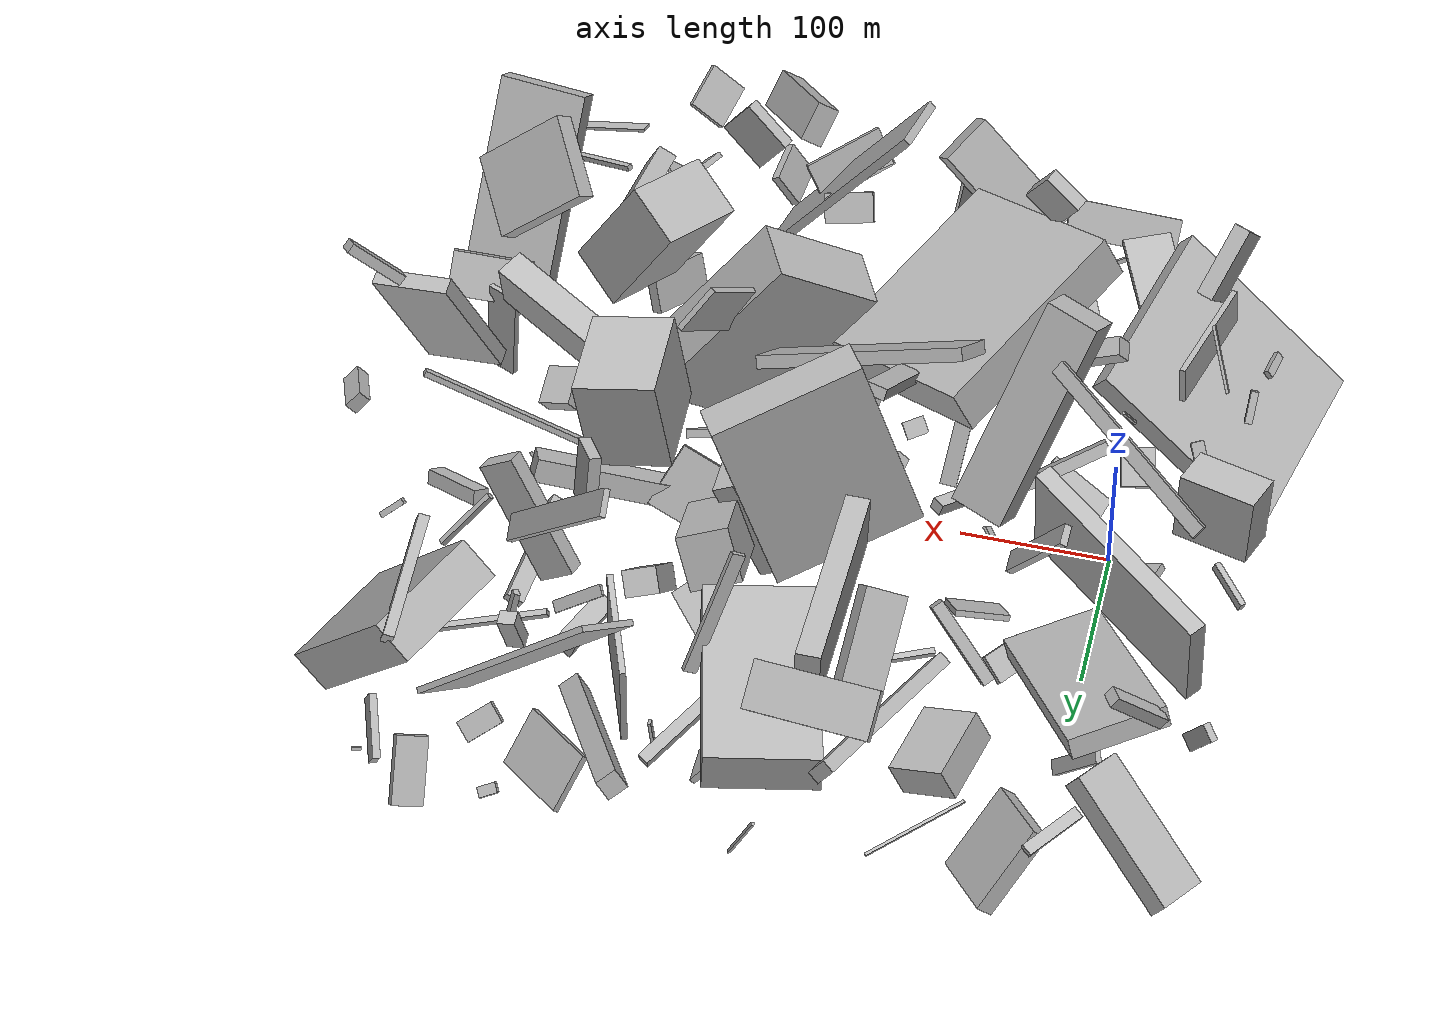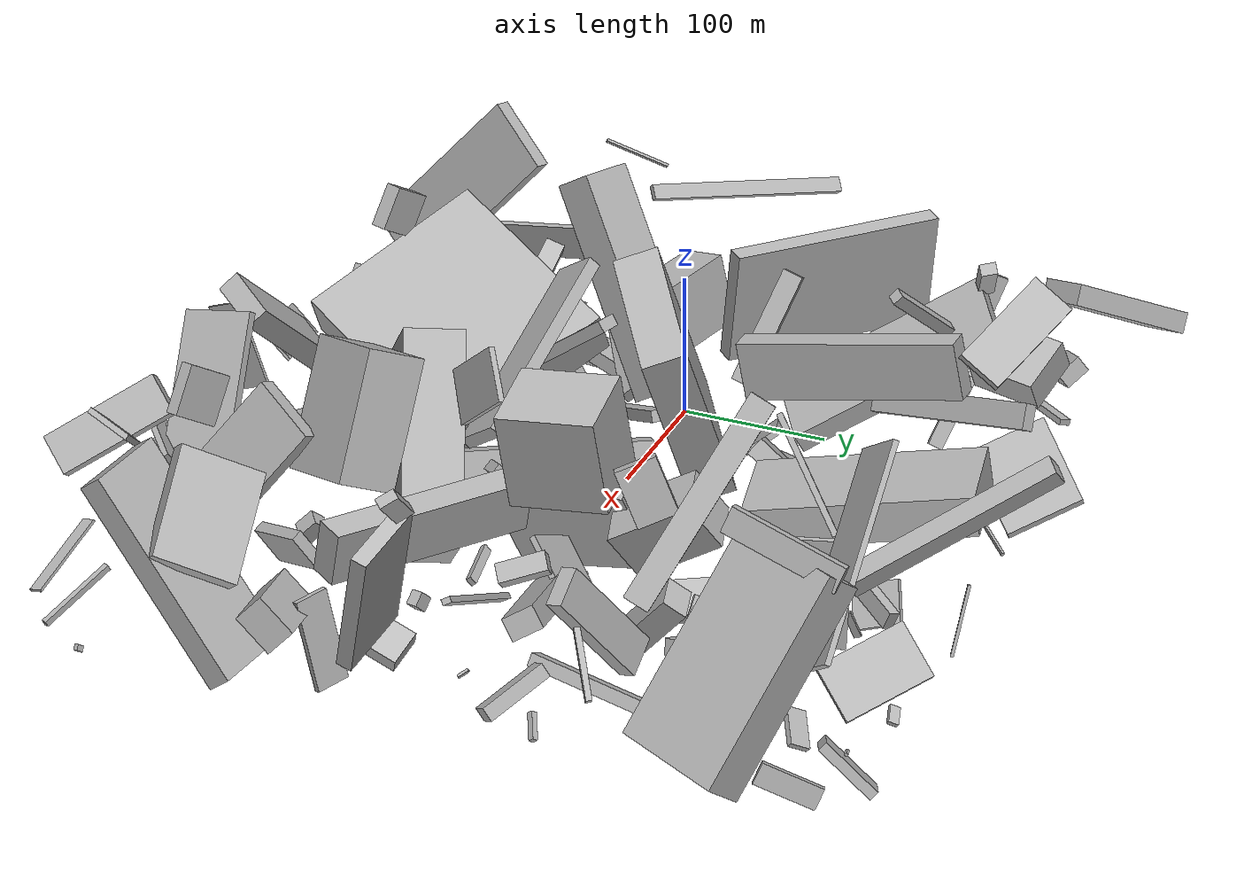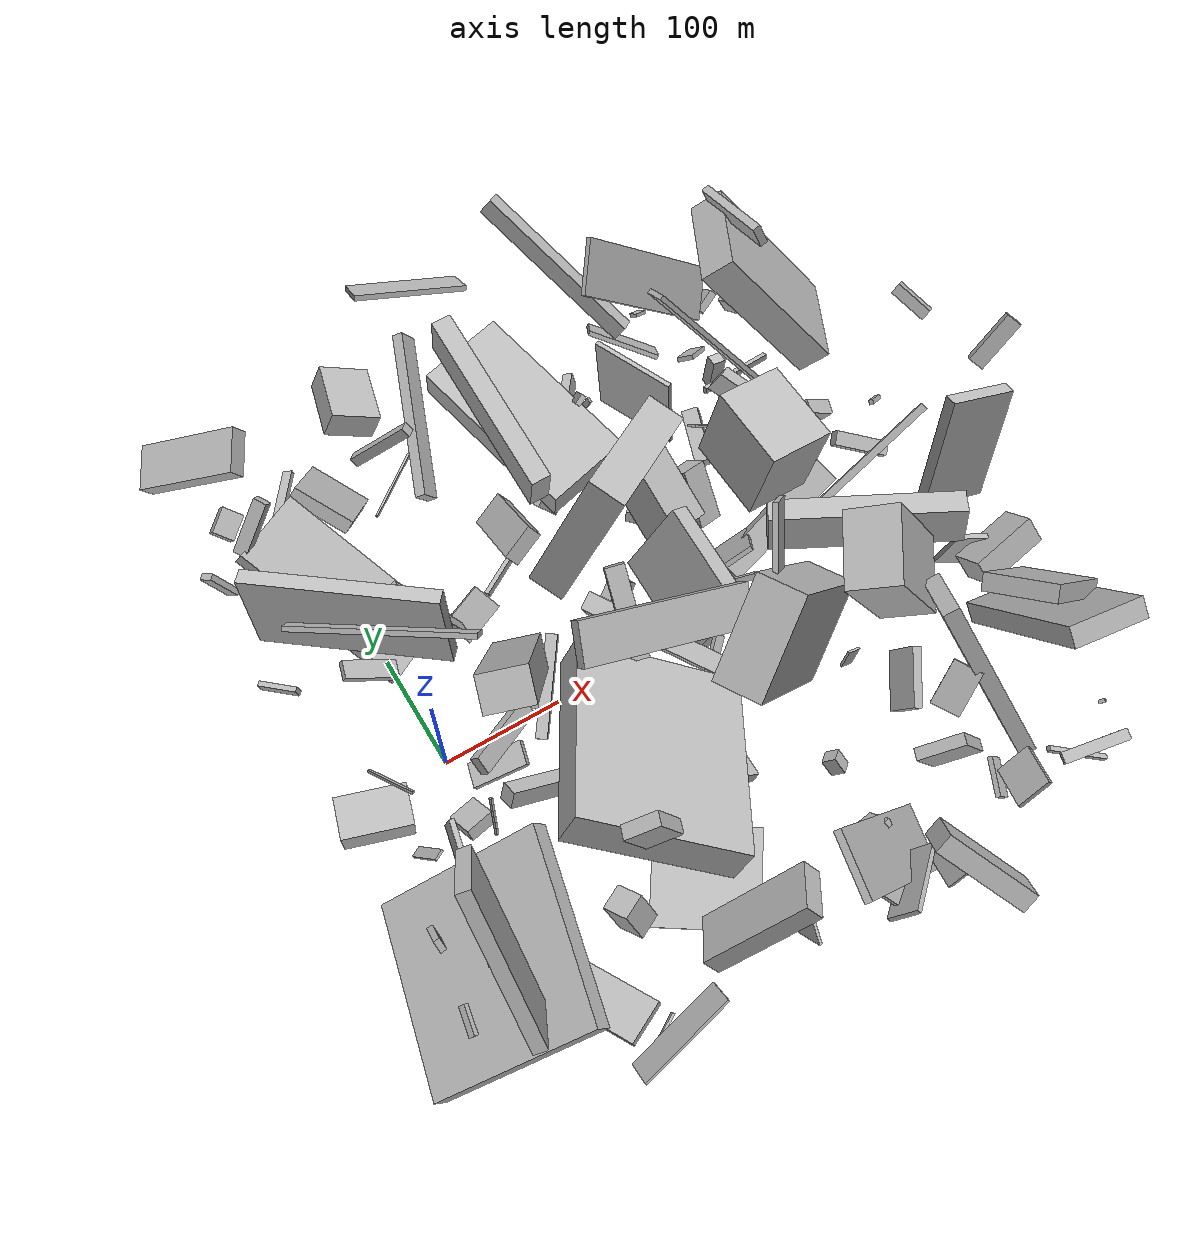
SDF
<sdf version="1.6">
 <world name="default">
  <scene>
   <sky><clouds><speed>12</speed></clouds></sky>
   <ambient>0.4 0.4 0.4 1</ambient>
   <background>0.7 0.7 0.7 1</background>
   <shadows>1</shadows>
  </scene>
  <gravity>0 0 -9.8066</gravity>
  <magnetic_field>6e-06 2.3e-05 -4.2e-05</magnetic_field>
  <physics default="0" name="default_physics" type="ode">
   <ode>
    <solver>
     <type>quick</type>
     <iters>10</iters>
     <sor>1.0</sor>
     <use_dynamic_moi_rescaling>0</use_dynamic_moi_rescaling>
    </solver>
    <constraints>
     <cfm>0</cfm>
     <erp>0.2</erp>
     <contact_max_correcting_vel>100</contact_max_correcting_vel>
     <contact_surface_layer>0.001</contact_surface_layer>
    </constraints>
   </ode>
   <max_step_size>0.004</max_step_size>
   <real_time_factor>1</real_time_factor>
   <real_time_update_rate>250</real_time_update_rate>
  </physics>
  <light name="sun" type="directional">
   <pose>0 0 10 0 0 0</pose>
   <diffuse>0.8 0.8 0.8 1</diffuse>
   <specular>0.2 0.2 0.2 1</specular>
   <attenuation>
    <range>1000</range>
    <constant>0.9</constant>
    <linear>0.01</linear>
    <quadratic>0.001</quadratic>
   </attenuation>
   <direction>-0.5 0.1 -0.9</direction>
  </light>
  <model name="building_1">
   <static>0</static>
   <pose>247.25564616572376 14.462113491345617 75.60430960370272 -2.9635172434130266 0.45295531011546103 0.08792647730640184</pose>
   <link name="link">
    <gravity>0</gravity>
    <pose>0 0 38.0 0 0 0</pose>
    <collision name="collision"><geometry><box><size>15 94 76</size></box></geometry></collision>
    <visual name="visual">
     <cast_shadows>0</cast_shadows>
     <geometry><box><size>15 94 76</size></box></geometry>
     <material>
      <script>
       <uri>model://HANNAS_wall/materials/scripts</uri>
       <uri>model://HANNAS_wall/materials/textures</uri>
       <name>vrc/HANNAS_wall</name>
      </script>
     </material>
    </visual>
   </link>
  </model>
  <model name="building_2">
   <static>0</static>
   <pose>-43.06416409679491 -35.29537906546936 41.528346216033526 1.5122327611272661 0.2192334558442204 -1.8726367923088598</pose>
   <link name="link">
    <gravity>0</gravity>
    <pose>0 0 26.5 0 0 0</pose>
    <collision name="collision"><geometry><box><size>31 48 53</size></box></geometry></collision>
    <visual name="visual">
     <cast_shadows>0</cast_shadows>
     <geometry><box><size>31 48 53</size></box></geometry>
     <material>
      <script>
       <uri>model://HANNAS_wall/materials/scripts</uri>
       <uri>model://HANNAS_wall/materials/textures</uri>
       <name>vrc/HANNAS_wall</name>
      </script>
     </material>
    </visual>
   </link>
  </model>
  <model name="building_3">
   <static>0</static>
   <pose>11.928828027424181 -172.6298789571358 54.83418452722762 -3.041463361954685 0.9452411731629204 -0.14230768062275148</pose>
   <link name="link">
    <gravity>0</gravity>
    <pose>0 0 75.0 0 0 0</pose>
    <collision name="collision"><geometry><box><size>15 150 150</size></box></geometry></collision>
    <visual name="visual">
     <cast_shadows>0</cast_shadows>
     <geometry><box><size>15 150 150</size></box></geometry>
     <material>
      <script>
       <uri>model://HANNAS_wall/materials/scripts</uri>
       <uri>model://HANNAS_wall/materials/textures</uri>
       <name>vrc/HANNAS_wall</name>
      </script>
     </material>
    </visual>
   </link>
  </model>
  <model name="building_4">
   <static>0</static>
   <pose>184.66313208969285 -252.12507988119435 114.79458210587899 2.497440499912522 -0.24296751222006827 1.4240888975236907</pose>
   <link name="link">
    <gravity>0</gravity>
    <pose>0 0 75.0 0 0 0</pose>
    <collision name="collision"><geometry><box><size>52 6 150</size></box></geometry></collision>
    <visual name="visual">
     <cast_shadows>0</cast_shadows>
     <geometry><box><size>52 6 150</size></box></geometry>
     <material>
      <script>
       <uri>model://HANNAS_wall/materials/scripts</uri>
       <uri>model://HANNAS_wall/materials/textures</uri>
       <name>vrc/HANNAS_wall</name>
      </script>
     </material>
    </visual>
   </link>
  </model>
  <model name="building_5">
   <static>0</static>
   <pose>289.2142373373566 114.487340648304 39.522468649719194 -2.847032237965067 0.6554458507236693 1.9828597212272638</pose>
   <link name="link">
    <gravity>0</gravity>
    <pose>0 0 25.5 0 0 0</pose>
    <collision name="collision"><geometry><box><size>18 23 51</size></box></geometry></collision>
    <visual name="visual">
     <cast_shadows>0</cast_shadows>
     <geometry><box><size>18 23 51</size></box></geometry>
     <material>
      <script>
       <uri>model://HANNAS_wall/materials/scripts</uri>
       <uri>model://HANNAS_wall/materials/textures</uri>
       <name>vrc/HANNAS_wall</name>
      </script>
     </material>
    </visual>
   </link>
  </model>
  <model name="building_6">
   <static>0</static>
   <pose>258.01275105135267 -250.55222126186365 36.368019153706854 1.2348833315552048 -0.9316814360676532 -0.5921320384562274</pose>
   <link name="link">
    <gravity>0</gravity>
    <pose>0 0 28.5 0 0 0</pose>
    <collision name="collision"><geometry><box><size>29 4 57</size></box></geometry></collision>
    <visual name="visual">
     <cast_shadows>0</cast_shadows>
     <geometry><box><size>29 4 57</size></box></geometry>
     <material>
      <script>
       <uri>model://HANNAS_wall/materials/scripts</uri>
       <uri>model://HANNAS_wall/materials/textures</uri>
       <name>vrc/HANNAS_wall</name>
      </script>
     </material>
    </visual>
   </link>
  </model>
  <model name="building_7">
   <static>0</static>
   <pose>151.05791103725602 -18.51421171967675 129.4460728815901 2.471843062320055 0.056776454919606124 2.896279241501477</pose>
   <link name="link">
    <gravity>0</gravity>
    <pose>0 0 4.0 0 0 0</pose>
    <collision name="collision"><geometry><box><size>15 71 8</size></box></geometry></collision>
    <visual name="visual">
     <cast_shadows>0</cast_shadows>
     <geometry><box><size>15 71 8</size></box></geometry>
     <material>
      <script>
       <uri>model://HANNAS_wall/materials/scripts</uri>
       <uri>model://HANNAS_wall/materials/textures</uri>
       <name>vrc/HANNAS_wall</name>
      </script>
     </material>
    </visual>
   </link>
  </model>
  <model name="building_8">
   <static>0</static>
   <pose>286.3670632729056 189.67340590118386 58.65042328871326 -2.006356038778418 -1.519162268769796 2.370970248109026</pose>
   <link name="link">
    <gravity>0</gravity>
    <pose>0 0 2.0 0 0 0</pose>
    <collision name="collision"><geometry><box><size>77 75 4</size></box></geometry></collision>
    <visual name="visual">
     <cast_shadows>0</cast_shadows>
     <geometry><box><size>77 75 4</size></box></geometry>
     <material>
      <script>
       <uri>model://HANNAS_wall/materials/scripts</uri>
       <uri>model://HANNAS_wall/materials/textures</uri>
       <name>vrc/HANNAS_wall</name>
      </script>
     </material>
    </visual>
   </link>
  </model>
  <model name="building_9">
   <static>0</static>
   <pose>162.1933564102537 76.93561353719329 77.17163834129929 0.30598746392128373 0.23679884569680124 0.5829813841358437</pose>
   <link name="link">
    <gravity>0</gravity>
    <pose>0 0 63.5 0 0 0</pose>
    <collision name="collision"><geometry><box><size>103 30 127</size></box></geometry></collision>
    <visual name="visual">
     <cast_shadows>0</cast_shadows>
     <geometry><box><size>103 30 127</size></box></geometry>
     <material>
      <script>
       <uri>model://HANNAS_wall/materials/scripts</uri>
       <uri>model://HANNAS_wall/materials/textures</uri>
       <name>vrc/HANNAS_wall</name>
      </script>
     </material>
    </visual>
   </link>
  </model>
  <model name="building_10">
   <static>0</static>
   <pose>257.06418574378597 -159.6452081089494 14.557034561253264 2.7035507755042474 0.7687642819215498 -1.2164773075696198</pose>
   <link name="link">
    <gravity>0</gravity>
    <pose>0 0 6.0 0 0 0</pose>
    <collision name="collision"><geometry><box><size>15 11 12</size></box></geometry></collision>
    <visual name="visual">
     <cast_shadows>0</cast_shadows>
     <geometry><box><size>15 11 12</size></box></geometry>
     <material>
      <script>
       <uri>model://HANNAS_wall/materials/scripts</uri>
       <uri>model://HANNAS_wall/materials/textures</uri>
       <name>vrc/HANNAS_wall</name>
      </script>
     </material>
    </visual>
   </link>
  </model>
  <model name="building_11">
   <static>0</static>
   <pose>253.59817151545147 245.509929735574 33.314348179032564 -0.8123840279048146 -1.1819879248808915 1.7997221055847743</pose>
   <link name="link">
    <gravity>0</gravity>
    <pose>0 0 45.5 0 0 0</pose>
    <collision name="collision"><geometry><box><size>12 8 91</size></box></geometry></collision>
    <visual name="visual">
     <cast_shadows>0</cast_shadows>
     <geometry><box><size>12 8 91</size></box></geometry>
     <material>
      <script>
       <uri>model://HANNAS_wall/materials/scripts</uri>
       <uri>model://HANNAS_wall/materials/textures</uri>
       <name>vrc/HANNAS_wall</name>
      </script>
     </material>
    </visual>
   </link>
  </model>
  <model name="building_12">
   <static>0</static>
   <pose>187.52213046455998 204.89393665412254 64.36828580028632 -0.06006868556614837 -0.15044644811327174 1.820453800958363</pose>
   <link name="link">
    <gravity>0</gravity>
    <pose>0 0 13.5 0 0 0</pose>
    <collision name="collision"><geometry><box><size>150 74 27</size></box></geometry></collision>
    <visual name="visual">
     <cast_shadows>0</cast_shadows>
     <geometry><box><size>150 74 27</size></box></geometry>
     <material>
      <script>
       <uri>model://HANNAS_wall/materials/scripts</uri>
       <uri>model://HANNAS_wall/materials/textures</uri>
       <name>vrc/HANNAS_wall</name>
      </script>
     </material>
    </visual>
   </link>
  </model>
  <model name="building_13">
   <static>0</static>
   <pose>18.78002924352293 159.93461330873617 58.31733415195606 1.3397520099223323 -1.061775750951858 -0.8187858555109614</pose>
   <link name="link">
    <gravity>0</gravity>
    <pose>0 0 32.5 0 0 0</pose>
    <collision name="collision"><geometry><box><size>14 150 65</size></box></geometry></collision>
    <visual name="visual">
     <cast_shadows>0</cast_shadows>
     <geometry><box><size>14 150 65</size></box></geometry>
     <material>
      <script>
       <uri>model://HANNAS_wall/materials/scripts</uri>
       <uri>model://HANNAS_wall/materials/textures</uri>
       <name>vrc/HANNAS_wall</name>
      </script>
     </material>
    </visual>
   </link>
  </model>
  <model name="building_14">
   <static>0</static>
   <pose>365.4577114656404 -172.82161058765564 93.7542082871282 2.026593120078339 -0.5094875937602538 -1.970106211122446</pose>
   <link name="link">
    <gravity>0</gravity>
    <pose>0 0 6.5 0 0 0</pose>
    <collision name="collision"><geometry><box><size>47 150 13</size></box></geometry></collision>
    <visual name="visual">
     <cast_shadows>0</cast_shadows>
     <geometry><box><size>47 150 13</size></box></geometry>
     <material>
      <script>
       <uri>model://HANNAS_wall/materials/scripts</uri>
       <uri>model://HANNAS_wall/materials/textures</uri>
       <name>vrc/HANNAS_wall</name>
      </script>
     </material>
    </visual>
   </link>
  </model>
  <model name="building_15">
   <static>0</static>
   <pose>166.66447459969282 -50.158923373551104 114.08801284935214 0.5822090159343414 0.8071801652249878 1.942691280613736</pose>
   <link name="link">
    <gravity>0</gravity>
    <pose>0 0 17.0 0 0 0</pose>
    <collision name="collision"><geometry><box><size>9 150 34</size></box></geometry></collision>
    <visual name="visual">
     <cast_shadows>0</cast_shadows>
     <geometry><box><size>9 150 34</size></box></geometry>
     <material>
      <script>
       <uri>model://HANNAS_wall/materials/scripts</uri>
       <uri>model://HANNAS_wall/materials/textures</uri>
       <name>vrc/HANNAS_wall</name>
      </script>
     </material>
    </visual>
   </link>
  </model>
  <model name="building_16">
   <static>0</static>
   <pose>264.9657299309158 -90.58075863397164 92.11444260810967 -1.675676537992185 -0.679868431199056 0.5538428903663807</pose>
   <link name="link">
    <gravity>0</gravity>
    <pose>0 0 20.0 0 0 0</pose>
    <collision name="collision"><geometry><box><size>85 137 40</size></box></geometry></collision>
    <visual name="visual">
     <cast_shadows>0</cast_shadows>
     <geometry><box><size>85 137 40</size></box></geometry>
     <material>
      <script>
       <uri>model://HANNAS_wall/materials/scripts</uri>
       <uri>model://HANNAS_wall/materials/textures</uri>
       <name>vrc/HANNAS_wall</name>
      </script>
     </material>
    </visual>
   </link>
  </model>
  <model name="building_17">
   <static>0</static>
   <pose>81.33989562827404 168.13628327267443 87.74620029043935 1.0449991332170956 -0.9931294400301272 -3.0600626239854867</pose>
   <link name="link">
    <gravity>0</gravity>
    <pose>0 0 67.5 0 0 0</pose>
    <collision name="collision"><geometry><box><size>17 9 135</size></box></geometry></collision>
    <visual name="visual">
     <cast_shadows>0</cast_shadows>
     <geometry><box><size>17 9 135</size></box></geometry>
     <material>
      <script>
       <uri>model://HANNAS_wall/materials/scripts</uri>
       <uri>model://HANNAS_wall/materials/textures</uri>
       <name>vrc/HANNAS_wall</name>
      </script>
     </material>
    </visual>
   </link>
  </model>
  <model name="building_18">
   <static>0</static>
   <pose>405.32095406356575 175.27557718189587 92.2579783834339 1.666528057148727 -0.916146421783114 2.6066922761956195</pose>
   <link name="link">
    <gravity>0</gravity>
    <pose>0 0 40.0 0 0 0</pose>
    <collision name="collision"><geometry><box><size>150 30 80</size></box></geometry></collision>
    <visual name="visual">
     <cast_shadows>0</cast_shadows>
     <geometry><box><size>150 30 80</size></box></geometry>
     <material>
      <script>
       <uri>model://HANNAS_wall/materials/scripts</uri>
       <uri>model://HANNAS_wall/materials/textures</uri>
       <name>vrc/HANNAS_wall</name>
      </script>
     </material>
    </visual>
   </link>
  </model>
  <model name="building_19">
   <static>0</static>
   <pose>331.62193043753535 -237.3276081575605 52.84120009543262 2.8828233184658347 0.6751338213556818 2.576929909826259</pose>
   <link name="link">
    <gravity>0</gravity>
    <pose>0 0 6.5 0 0 0</pose>
    <collision name="collision"><geometry><box><size>4 30 13</size></box></geometry></collision>
    <visual name="visual">
     <cast_shadows>0</cast_shadows>
     <geometry><box><size>4 30 13</size></box></geometry>
     <material>
      <script>
       <uri>model://HANNAS_wall/materials/scripts</uri>
       <uri>model://HANNAS_wall/materials/textures</uri>
       <name>vrc/HANNAS_wall</name>
      </script>
     </material>
    </visual>
   </link>
  </model>
  <model name="building_20">
   <static>0</static>
   <pose>165.10369536017404 -146.79498748725783 76.10419049208906 1.1660008790077596 -0.2176925827850845 -2.098831883526979</pose>
   <link name="link">
    <gravity>0</gravity>
    <pose>0 0 65.0 0 0 0</pose>
    <collision name="collision"><geometry><box><size>150 31 130</size></box></geometry></collision>
    <visual name="visual">
     <cast_shadows>0</cast_shadows>
     <geometry><box><size>150 31 130</size></box></geometry>
     <material>
      <script>
       <uri>model://HANNAS_wall/materials/scripts</uri>
       <uri>model://HANNAS_wall/materials/textures</uri>
       <name>vrc/HANNAS_wall</name>
      </script>
     </material>
    </visual>
   </link>
  </model>
  <model name="building_21">
   <static>0</static>
   <pose>348.7674322110413 -90.00247538912689 110.13595327684546 0.2784326214724259 -0.43303446359213504 -0.6743469586234977</pose>
   <link name="link">
    <gravity>0</gravity>
    <pose>0 0 43.5 0 0 0</pose>
    <collision name="collision"><geometry><box><size>42 59 87</size></box></geometry></collision>
    <visual name="visual">
     <cast_shadows>0</cast_shadows>
     <geometry><box><size>42 59 87</size></box></geometry>
     <material>
      <script>
       <uri>model://HANNAS_wall/materials/scripts</uri>
       <uri>model://HANNAS_wall/materials/textures</uri>
       <name>vrc/HANNAS_wall</name>
      </script>
     </material>
    </visual>
   </link>
  </model>
  <model name="building_22">
   <static>0</static>
   <pose>463.54089736277245 89.01485244951323 35.96948320459614 -0.7432093810470143 -0.5842371511405798 -0.6461628118480872</pose>
   <link name="link">
    <gravity>0</gravity>
    <pose>0 0 2.0 0 0 0</pose>
    <collision name="collision"><geometry><box><size>4 19 4</size></box></geometry></collision>
    <visual name="visual">
     <cast_shadows>0</cast_shadows>
     <geometry><box><size>4 19 4</size></box></geometry>
     <material>
      <script>
       <uri>model://HANNAS_wall/materials/scripts</uri>
       <uri>model://HANNAS_wall/materials/textures</uri>
       <name>vrc/HANNAS_wall</name>
      </script>
     </material>
    </visual>
   </link>
  </model>
  <model name="building_23">
   <static>0</static>
   <pose>188.87959244652018 -25.453957033487313 5.468533106784075 1.3021868661032523 -0.20822001082450298 -2.5868284031259967</pose>
   <link name="link">
    <gravity>0</gravity>
    <pose>0 0 4.5 0 0 0</pose>
    <collision name="collision"><geometry><box><size>4 4 9</size></box></geometry></collision>
    <visual name="visual">
     <cast_shadows>0</cast_shadows>
     <geometry><box><size>4 4 9</size></box></geometry>
     <material>
      <script>
       <uri>model://HANNAS_wall/materials/scripts</uri>
       <uri>model://HANNAS_wall/materials/textures</uri>
       <name>vrc/HANNAS_wall</name>
      </script>
     </material>
    </visual>
   </link>
  </model>
  <model name="building_24">
   <static>0</static>
   <pose>118.08836414888549 -185.036406015912 20.844108270170324 3.1211803563545706 -0.2418961866104487 0.9813084830571864</pose>
   <link name="link">
    <gravity>0</gravity>
    <pose>0 0 2.0 0 0 0</pose>
    <collision name="collision"><geometry><box><size>75 81 4</size></box></geometry></collision>
    <visual name="visual">
     <cast_shadows>0</cast_shadows>
     <geometry><box><size>75 81 4</size></box></geometry>
     <material>
      <script>
       <uri>model://HANNAS_wall/materials/scripts</uri>
       <uri>model://HANNAS_wall/materials/textures</uri>
       <name>vrc/HANNAS_wall</name>
      </script>
     </material>
    </visual>
   </link>
  </model>
  <model name="building_25">
   <static>0</static>
   <pose>-18.812848995216726 91.54447209559609 67.65528679205451 -0.049518898031811406 0.0791245015229284 0.88316561202585</pose>
   <link name="link">
    <gravity>0</gravity>
    <pose>0 0 39.0 0 0 0</pose>
    <collision name="collision"><geometry><box><size>12 150 78</size></box></geometry></collision>
    <visual name="visual">
     <cast_shadows>0</cast_shadows>
     <geometry><box><size>12 150 78</size></box></geometry>
     <material>
      <script>
       <uri>model://HANNAS_wall/materials/scripts</uri>
       <uri>model://HANNAS_wall/materials/textures</uri>
       <name>vrc/HANNAS_wall</name>
      </script>
     </material>
    </visual>
   </link>
  </model>
  <model name="building_26">
   <static>0</static>
   <pose>429.467461839679 249.96679776245674 21.223879239739812 -2.7088779864834422 0.227681322237212 -2.7192113132853972</pose>
   <link name="link">
    <gravity>0</gravity>
    <pose>0 0 7.5 0 0 0</pose>
    <collision name="collision"><geometry><box><size>5 42 15</size></box></geometry></collision>
    <visual name="visual">
     <cast_shadows>0</cast_shadows>
     <geometry><box><size>5 42 15</size></box></geometry>
     <material>
      <script>
       <uri>model://HANNAS_wall/materials/scripts</uri>
       <uri>model://HANNAS_wall/materials/textures</uri>
       <name>vrc/HANNAS_wall</name>
      </script>
     </material>
    </visual>
   </link>
  </model>
  <model name="building_27">
   <static>0</static>
   <pose>-40.38937221366661 67.6825734378724 86.49796692367192 2.1183583569414957 -0.10256188822992289 1.2975595576226358</pose>
   <link name="link">
    <gravity>0</gravity>
    <pose>0 0 22.0 0 0 0</pose>
    <collision name="collision"><geometry><box><size>15 5 44</size></box></geometry></collision>
    <visual name="visual">
     <cast_shadows>0</cast_shadows>
     <geometry><box><size>15 5 44</size></box></geometry>
     <material>
      <script>
       <uri>model://HANNAS_wall/materials/scripts</uri>
       <uri>model://HANNAS_wall/materials/textures</uri>
       <name>vrc/HANNAS_wall</name>
      </script>
     </material>
    </visual>
   </link>
  </model>
  <model name="building_28">
   <static>0</static>
   <pose>149.3635318021911 -5.051774859937405 52.0594634591486 1.1735915217077801 -0.7577960298756012 -0.0011925724624790993</pose>
   <link name="link">
    <gravity>0</gravity>
    <pose>0 0 4.5 0 0 0</pose>
    <collision name="collision"><geometry><box><size>10 16 9</size></box></geometry></collision>
    <visual name="visual">
     <cast_shadows>0</cast_shadows>
     <geometry><box><size>10 16 9</size></box></geometry>
     <material>
      <script>
       <uri>model://HANNAS_wall/materials/scripts</uri>
       <uri>model://HANNAS_wall/materials/textures</uri>
       <name>vrc/HANNAS_wall</name>
      </script>
     </material>
    </visual>
   </link>
  </model>
  <model name="building_29">
   <static>0</static>
   <pose>42.18784823916815 -88.02646242473921 102.62921909263567 2.6035690352583547 -0.33607967526793325 -1.4269190226014843</pose>
   <link name="link">
    <gravity>0</gravity>
    <pose>0 0 6.5 0 0 0</pose>
    <collision name="collision"><geometry><box><size>13 61 13</size></box></geometry></collision>
    <visual name="visual">
     <cast_shadows>0</cast_shadows>
     <geometry><box><size>13 61 13</size></box></geometry>
     <material>
      <script>
       <uri>model://HANNAS_wall/materials/scripts</uri>
       <uri>model://HANNAS_wall/materials/textures</uri>
       <name>vrc/HANNAS_wall</name>
      </script>
     </material>
    </visual>
   </link>
  </model>
  <model name="building_30">
   <static>0</static>
   <pose>409.2623093775884 -250.41735914155933 23.585346520486343 -1.5155799600463071 0.4397689259994023 -0.4874812544959937</pose>
   <link name="link">
    <gravity>0</gravity>
    <pose>0 0 2.0 0 0 0</pose>
    <collision name="collision"><geometry><box><size>55 4 4</size></box></geometry></collision>
    <visual name="visual">
     <cast_shadows>0</cast_shadows>
     <geometry><box><size>55 4 4</size></box></geometry>
     <material>
      <script>
       <uri>model://HANNAS_wall/materials/scripts</uri>
       <uri>model://HANNAS_wall/materials/textures</uri>
       <name>vrc/HANNAS_wall</name>
      </script>
     </material>
    </visual>
   </link>
  </model>
  <model name="building_31">
   <static>0</static>
   <pose>251.30746644366687 106.0294677410221 17.5369636872994 2.708077214649187 -0.09728091228997875 -0.8689740727330924</pose>
   <link name="link">
    <gravity>0</gravity>
    <pose>0 0 4.5 0 0 0</pose>
    <collision name="collision"><geometry><box><size>36 28 9</size></box></geometry></collision>
    <visual name="visual">
     <cast_shadows>0</cast_shadows>
     <geometry><box><size>36 28 9</size></box></geometry>
     <material>
      <script>
       <uri>model://HANNAS_wall/materials/scripts</uri>
       <uri>model://HANNAS_wall/materials/textures</uri>
       <name>vrc/HANNAS_wall</name>
      </script>
     </material>
    </visual>
   </link>
  </model>
  <model name="building_32">
   <static>0</static>
   <pose>378.3920067391892 46.734617768199385 53.5950499401965 -1.919837449566748 -0.5011555213389833 1.9584101541867578</pose>
   <link name="link">
    <gravity>0</gravity>
    <pose>0 0 57.0 0 0 0</pose>
    <collision name="collision"><geometry><box><size>22 16 114</size></box></geometry></collision>
    <visual name="visual">
     <cast_shadows>0</cast_shadows>
     <geometry><box><size>22 16 114</size></box></geometry>
     <material>
      <script>
       <uri>model://HANNAS_wall/materials/scripts</uri>
       <uri>model://HANNAS_wall/materials/textures</uri>
       <name>vrc/HANNAS_wall</name>
      </script>
     </material>
    </visual>
   </link>
  </model>
  <model name="building_33">
   <static>0</static>
   <pose>-50.37000111207336 -197.93923310095994 124.2868056558377 2.807359975993759 -0.8647878269445229 1.5696627818383009</pose>
   <link name="link">
    <gravity>0</gravity>
    <pose>0 0 25.5 0 0 0</pose>
    <collision name="collision"><geometry><box><size>136 11 51</size></box></geometry></collision>
    <visual name="visual">
     <cast_shadows>0</cast_shadows>
     <geometry><box><size>136 11 51</size></box></geometry>
     <material>
      <script>
       <uri>model://HANNAS_wall/materials/scripts</uri>
       <uri>model://HANNAS_wall/materials/textures</uri>
       <name>vrc/HANNAS_wall</name>
      </script>
     </material>
    </visual>
   </link>
  </model>
  <model name="building_34">
   <static>0</static>
   <pose>89.07675994336454 90.67669817633858 42.00629178556375 -1.9272594793093878 -0.5882406558450742 2.0949694536409105</pose>
   <link name="link">
    <gravity>0</gravity>
    <pose>0 0 18.5 0 0 0</pose>
    <collision name="collision"><geometry><box><size>25 4 37</size></box></geometry></collision>
    <visual name="visual">
     <cast_shadows>0</cast_shadows>
     <geometry><box><size>25 4 37</size></box></geometry>
     <material>
      <script>
       <uri>model://HANNAS_wall/materials/scripts</uri>
       <uri>model://HANNAS_wall/materials/textures</uri>
       <name>vrc/HANNAS_wall</name>
      </script>
     </material>
    </visual>
   </link>
  </model>
  <model name="building_35">
   <static>0</static>
   <pose>56.791031017421346 258.1897175253935 112.3007640568006 0.45227282718743594 0.022849789833979197 1.3300063151947592</pose>
   <link name="link">
    <gravity>0</gravity>
    <pose>0 0 11.5 0 0 0</pose>
    <collision name="collision"><geometry><box><size>49 39 23</size></box></geometry></collision>
    <visual name="visual">
     <cast_shadows>0</cast_shadows>
     <geometry><box><size>49 39 23</size></box></geometry>
     <material>
      <script>
       <uri>model://HANNAS_wall/materials/scripts</uri>
       <uri>model://HANNAS_wall/materials/textures</uri>
       <name>vrc/HANNAS_wall</name>
      </script>
     </material>
    </visual>
   </link>
  </model>
  <model name="building_36">
   <static>0</static>
   <pose>471.3837288821501 8.707934691546987 173.85690534004857 -0.621487582269368 -0.618373364829823 -2.136584592025859</pose>
   <link name="link">
    <gravity>0</gravity>
    <pose>0 0 21.0 0 0 0</pose>
    <collision name="collision"><geometry><box><size>7 13 42</size></box></geometry></collision>
    <visual name="visual">
     <cast_shadows>0</cast_shadows>
     <geometry><box><size>7 13 42</size></box></geometry>
     <material>
      <script>
       <uri>model://HANNAS_wall/materials/scripts</uri>
       <uri>model://HANNAS_wall/materials/textures</uri>
       <name>vrc/HANNAS_wall</name>
      </script>
     </material>
    </visual>
   </link>
  </model>
  <model name="building_37">
   <static>0</static>
   <pose>299.2673876512058 233.6726550322296 82.57154157676685 0.9837995325255778 -0.3812498785156166 -2.4317050497325856</pose>
   <link name="link">
    <gravity>0</gravity>
    <pose>0 0 75.0 0 0 0</pose>
    <collision name="collision"><geometry><box><size>14 14 150</size></box></geometry></collision>
    <visual name="visual">
     <cast_shadows>0</cast_shadows>
     <geometry><box><size>14 14 150</size></box></geometry>
     <material>
      <script>
       <uri>model://HANNAS_wall/materials/scripts</uri>
       <uri>model://HANNAS_wall/materials/textures</uri>
       <name>vrc/HANNAS_wall</name>
      </script>
     </material>
    </visual>
   </link>
  </model>
  <model name="building_38">
   <static>0</static>
   <pose>366.28107424971716 87.92768621640694 58.42611993978048 -1.1334995149552503 -0.8994942217542045 -0.5869380719809292</pose>
   <link name="link">
    <gravity>0</gravity>
    <pose>0 0 6.0 0 0 0</pose>
    <collision name="collision"><geometry><box><size>88 27 12</size></box></geometry></collision>
    <visual name="visual">
     <cast_shadows>0</cast_shadows>
     <geometry><box><size>88 27 12</size></box></geometry>
     <material>
      <script>
       <uri>model://HANNAS_wall/materials/scripts</uri>
       <uri>model://HANNAS_wall/materials/textures</uri>
       <name>vrc/HANNAS_wall</name>
      </script>
     </material>
    </visual>
   </link>
  </model>
  <model name="building_39">
   <static>0</static>
   <pose>315.33818773237783 258.59615858503804 33.65368959097306 2.3748529100059126 0.29755600461227183 -0.7384300951666917</pose>
   <link name="link">
    <gravity>0</gravity>
    <pose>0 0 2.0 0 0 0</pose>
    <collision name="collision"><geometry><box><size>63 40 4</size></box></geometry></collision>
    <visual name="visual">
     <cast_shadows>0</cast_shadows>
     <geometry><box><size>63 40 4</size></box></geometry>
     <material>
      <script>
       <uri>model://HANNAS_wall/materials/scripts</uri>
       <uri>model://HANNAS_wall/materials/textures</uri>
       <name>vrc/HANNAS_wall</name>
      </script>
     </material>
    </visual>
   </link>
  </model>
  <model name="building_40">
   <static>0</static>
   <pose>183.9116080784965 148.46586532553624 15.8557910608599 -0.5326970400177579 0.3552214829469265 1.8686910778129449</pose>
   <link name="link">
    <gravity>0</gravity>
    <pose>0 0 12.0 0 0 0</pose>
    <collision name="collision"><geometry><box><size>7 11 24</size></box></geometry></collision>
    <visual name="visual">
     <cast_shadows>0</cast_shadows>
     <geometry><box><size>7 11 24</size></box></geometry>
     <material>
      <script>
       <uri>model://HANNAS_wall/materials/scripts</uri>
       <uri>model://HANNAS_wall/materials/textures</uri>
       <name>vrc/HANNAS_wall</name>
      </script>
     </material>
    </visual>
   </link>
  </model>
  <model name="building_41">
   <static>0</static>
   <pose>119.9713107308157 118.5299907396188 16.669516553121223 -1.798482153867741 -0.13117734687985574 0.5130513707406217</pose>
   <link name="link">
    <gravity>0</gravity>
    <pose>0 0 2.0 0 0 0</pose>
    <collision name="collision"><geometry><box><size>54 5 4</size></box></geometry></collision>
    <visual name="visual">
     <cast_shadows>0</cast_shadows>
     <geometry><box><size>54 5 4</size></box></geometry>
     <material>
      <script>
       <uri>model://HANNAS_wall/materials/scripts</uri>
       <uri>model://HANNAS_wall/materials/textures</uri>
       <name>vrc/HANNAS_wall</name>
      </script>
     </material>
    </visual>
   </link>
  </model>
  <model name="building_42">
   <static>0</static>
   <pose>261.11567225328395 94.03048547250748 59.158541309429374 -1.2581169457684724 -0.5356005235111225 1.6756028678406902</pose>
   <link name="link">
    <gravity>0</gravity>
    <pose>0 0 17.5 0 0 0</pose>
    <collision name="collision"><geometry><box><size>63 38 35</size></box></geometry></collision>
    <visual name="visual">
     <cast_shadows>0</cast_shadows>
     <geometry><box><size>63 38 35</size></box></geometry>
     <material>
      <script>
       <uri>model://HANNAS_wall/materials/scripts</uri>
       <uri>model://HANNAS_wall/materials/textures</uri>
       <name>vrc/HANNAS_wall</name>
      </script>
     </material>
    </visual>
   </link>
  </model>
  <model name="building_43">
   <static>0</static>
   <pose>11.707797125586406 232.54317961684538 37.52165092603536 2.6131032191943184 0.731236870645216 -2.9013333451660595</pose>
   <link name="link">
    <gravity>0</gravity>
    <pose>0 0 30.5 0 0 0</pose>
    <collision name="collision"><geometry><box><size>12 54 61</size></box></geometry></collision>
    <visual name="visual">
     <cast_shadows>0</cast_shadows>
     <geometry><box><size>12 54 61</size></box></geometry>
     <material>
      <script>
       <uri>model://HANNAS_wall/materials/scripts</uri>
       <uri>model://HANNAS_wall/materials/textures</uri>
       <name>vrc/HANNAS_wall</name>
      </script>
     </material>
    </visual>
   </link>
  </model>
  <model name="building_44">
   <static>0</static>
   <pose>155.53332905108988 176.45139938329316 147.00198913074598 1.663688213078426 -1.3678467157275211 -1.6498588888812595</pose>
   <link name="link">
    <gravity>0</gravity>
    <pose>0 0 8.0 0 0 0</pose>
    <collision name="collision"><geometry><box><size>39 150 16</size></box></geometry></collision>
    <visual name="visual">
     <cast_shadows>0</cast_shadows>
     <geometry><box><size>39 150 16</size></box></geometry>
     <material>
      <script>
       <uri>model://HANNAS_wall/materials/scripts</uri>
       <uri>model://HANNAS_wall/materials/textures</uri>
       <name>vrc/HANNAS_wall</name>
      </script>
     </material>
    </visual>
   </link>
  </model>
  <model name="building_45">
   <static>0</static>
   <pose>330.1906876057585 -258.58791092358086 99.24793812504151 0.7561737498831763 -0.28453524830460564 -1.834385356601723</pose>
   <link name="link">
    <gravity>0</gravity>
    <pose>0 0 2.0 0 0 0</pose>
    <collision name="collision"><geometry><box><size>33 28 4</size></box></geometry></collision>
    <visual name="visual">
     <cast_shadows>0</cast_shadows>
     <geometry><box><size>33 28 4</size></box></geometry>
     <material>
      <script>
       <uri>model://HANNAS_wall/materials/scripts</uri>
       <uri>model://HANNAS_wall/materials/textures</uri>
       <name>vrc/HANNAS_wall</name>
      </script>
     </material>
    </visual>
   </link>
  </model>
  <model name="building_46">
   <static>0</static>
   <pose>371.5337982061027 120.45575892429878 80.79520716882539 -0.544083111459358 0.4539177477522626 1.6266103946777455</pose>
   <link name="link">
    <gravity>0</gravity>
    <pose>0 0 75.0 0 0 0</pose>
    <collision name="collision"><geometry><box><size>18 4 150</size></box></geometry></collision>
    <visual name="visual">
     <cast_shadows>0</cast_shadows>
     <geometry><box><size>18 4 150</size></box></geometry>
     <material>
      <script>
       <uri>model://HANNAS_wall/materials/scripts</uri>
       <uri>model://HANNAS_wall/materials/textures</uri>
       <name>vrc/HANNAS_wall</name>
      </script>
     </material>
    </visual>
   </link>
  </model>
  <model name="building_47">
   <static>0</static>
   <pose>455.22679072106143 -144.58369630946999 88.53114560039074 -0.5808260478303408 -0.6486195164482991 0.9135510967537239</pose>
   <link name="link">
    <gravity>0</gravity>
    <pose>0 0 37.5 0 0 0</pose>
    <collision name="collision"><geometry><box><size>14 58 75</size></box></geometry></collision>
    <visual name="visual">
     <cast_shadows>0</cast_shadows>
     <geometry><box><size>14 58 75</size></box></geometry>
     <material>
      <script>
       <uri>model://HANNAS_wall/materials/scripts</uri>
       <uri>model://HANNAS_wall/materials/textures</uri>
       <name>vrc/HANNAS_wall</name>
      </script>
     </material>
    </visual>
   </link>
  </model>
  <model name="building_48">
   <static>0</static>
   <pose>-81.09818195186477 179.35921145348462 69.96617328985677 -0.5124602821230488 -0.15608704968688372 0.7911296424136584</pose>
   <link name="link">
    <gravity>0</gravity>
    <pose>0 0 14.5 0 0 0</pose>
    <collision name="collision"><geometry><box><size>5 12 29</size></box></geometry></collision>
    <visual name="visual">
     <cast_shadows>0</cast_shadows>
     <geometry><box><size>5 12 29</size></box></geometry>
     <material>
      <script>
       <uri>model://HANNAS_wall/materials/scripts</uri>
       <uri>model://HANNAS_wall/materials/textures</uri>
       <name>vrc/HANNAS_wall</name>
      </script>
     </material>
    </visual>
   </link>
  </model>
  <model name="building_49">
   <static>0</static>
   <pose>51.85451126076477 -171.6029440386497 23.94007400052054 -0.08473145993148844 -1.106959371725571 2.1106472256454736</pose>
   <link name="link">
    <gravity>0</gravity>
    <pose>0 0 11.0 0 0 0</pose>
    <collision name="collision"><geometry><box><size>30 20 22</size></box></geometry></collision>
    <visual name="visual">
     <cast_shadows>0</cast_shadows>
     <geometry><box><size>30 20 22</size></box></geometry>
     <material>
      <script>
       <uri>model://HANNAS_wall/materials/scripts</uri>
       <uri>model://HANNAS_wall/materials/textures</uri>
       <name>vrc/HANNAS_wall</name>
      </script>
     </material>
    </visual>
   </link>
  </model>
  <model name="building_50">
   <static>0</static>
   <pose>381.9990353004755 -45.513074514839836 17.866411698278057 0.390935647062928 -0.42100439875815643 2.9326230268730615</pose>
   <link name="link">
    <gravity>0</gravity>
    <pose>0 0 6.0 0 0 0</pose>
    <collision name="collision"><geometry><box><size>25 27 12</size></box></geometry></collision>
    <visual name="visual">
     <cast_shadows>0</cast_shadows>
     <geometry><box><size>25 27 12</size></box></geometry>
     <material>
      <script>
       <uri>model://HANNAS_wall/materials/scripts</uri>
       <uri>model://HANNAS_wall/materials/textures</uri>
       <name>vrc/HANNAS_wall</name>
      </script>
     </material>
    </visual>
   </link>
  </model>
  <model name="building_51">
   <static>0</static>
   <pose>194.36180542182876 -21.818592648578857 37.29418165838637 0.005317849275152725 0.3605984642221144 -2.6105090727802627</pose>
   <link name="link">
    <gravity>0</gravity>
    <pose>0 0 14.5 0 0 0</pose>
    <collision name="collision"><geometry><box><size>15 150 29</size></box></geometry></collision>
    <visual name="visual">
     <cast_shadows>0</cast_shadows>
     <geometry><box><size>15 150 29</size></box></geometry>
     <material>
      <script>
       <uri>model://HANNAS_wall/materials/scripts</uri>
       <uri>model://HANNAS_wall/materials/textures</uri>
       <name>vrc/HANNAS_wall</name>
      </script>
     </material>
    </visual>
   </link>
  </model>
  <model name="building_52">
   <static>0</static>
   <pose>-13.740247487271716 184.34719747040322 33.2820896682487 -1.1132341987462364 -0.47178680195423484 -1.2462120250391016</pose>
   <link name="link">
    <gravity>0</gravity>
    <pose>0 0 2.0 0 0 0</pose>
    <collision name="collision"><geometry><box><size>10 52 4</size></box></geometry></collision>
    <visual name="visual">
     <cast_shadows>0</cast_shadows>
     <geometry><box><size>10 52 4</size></box></geometry>
     <material>
      <script>
       <uri>model://HANNAS_wall/materials/scripts</uri>
       <uri>model://HANNAS_wall/materials/textures</uri>
       <name>vrc/HANNAS_wall</name>
      </script>
     </material>
    </visual>
   </link>
  </model>
  <model name="building_53">
   <static>0</static>
   <pose>422.46195100738964 -66.9134303075443 102.5614080269164 1.6453114159032307 -0.1303402900222471 -2.1118048893734636</pose>
   <link name="link">
    <gravity>0</gravity>
    <pose>0 0 75.0 0 0 0</pose>
    <collision name="collision"><geometry><box><size>20 36 150</size></box></geometry></collision>
    <visual name="visual">
     <cast_shadows>0</cast_shadows>
     <geometry><box><size>20 36 150</size></box></geometry>
     <material>
      <script>
       <uri>model://HANNAS_wall/materials/scripts</uri>
       <uri>model://HANNAS_wall/materials/textures</uri>
       <name>vrc/HANNAS_wall</name>
      </script>
     </material>
    </visual>
   </link>
  </model>
  <model name="building_54">
   <static>0</static>
   <pose>275.94877089430133 -211.1969581363485 104.41898827226656 -0.9888658296522991 0.1295274139480752 -1.9203929691620638</pose>
   <link name="link">
    <gravity>0</gravity>
    <pose>0 0 18.5 0 0 0</pose>
    <collision name="collision"><geometry><box><size>9 34 37</size></box></geometry></collision>
    <visual name="visual">
     <cast_shadows>0</cast_shadows>
     <geometry><box><size>9 34 37</size></box></geometry>
     <material>
      <script>
       <uri>model://HANNAS_wall/materials/scripts</uri>
       <uri>model://HANNAS_wall/materials/textures</uri>
       <name>vrc/HANNAS_wall</name>
      </script>
     </material>
    </visual>
   </link>
  </model>
  <model name="building_55">
   <static>0</static>
   <pose>410.4647558987262 99.18252722009527 53.65258616327454 1.5723167616344047 -0.7396939122868391 -2.5264760769014734</pose>
   <link name="link">
    <gravity>0</gravity>
    <pose>0 0 2.0 0 0 0</pose>
    <collision name="collision"><geometry><box><size>48 4 4</size></box></geometry></collision>
    <visual name="visual">
     <cast_shadows>0</cast_shadows>
     <geometry><box><size>48 4 4</size></box></geometry>
     <material>
      <script>
       <uri>model://HANNAS_wall/materials/scripts</uri>
       <uri>model://HANNAS_wall/materials/textures</uri>
       <name>vrc/HANNAS_wall</name>
      </script>
     </material>
    </visual>
   </link>
  </model>
  <model name="building_56">
   <static>0</static>
   <pose>-54.07093009144697 243.41038400036166 50.02042232015305 -0.47012985876268215 0.9279443488047018 1.8872585080148483</pose>
   <link name="link">
    <gravity>0</gravity>
    <pose>0 0 9.0 0 0 0</pose>
    <collision name="collision"><geometry><box><size>12 22 18</size></box></geometry></collision>
    <visual name="visual">
     <cast_shadows>0</cast_shadows>
     <geometry><box><size>12 22 18</size></box></geometry>
     <material>
      <script>
       <uri>model://HANNAS_wall/materials/scripts</uri>
       <uri>model://HANNAS_wall/materials/textures</uri>
       <name>vrc/HANNAS_wall</name>
      </script>
     </material>
    </visual>
   </link>
  </model>
  <model name="building_57">
   <static>0</static>
   <pose>142.01096233073807 -56.98833805431559 22.74554374980105 0.932335480987537 0.18118007763292915 0.523214588447077</pose>
   <link name="link">
    <gravity>0</gravity>
    <pose>0 0 6.0 0 0 0</pose>
    <collision name="collision"><geometry><box><size>15 4 12</size></box></geometry></collision>
    <visual name="visual">
     <cast_shadows>0</cast_shadows>
     <geometry><box><size>15 4 12</size></box></geometry>
     <material>
      <script>
       <uri>model://HANNAS_wall/materials/scripts</uri>
       <uri>model://HANNAS_wall/materials/textures</uri>
       <name>vrc/HANNAS_wall</name>
      </script>
     </material>
    </visual>
   </link>
  </model>
  <model name="building_58">
   <static>0</static>
   <pose>373.9152919280259 170.7180401129542 48.285809987106674 -2.9203304285537093 -0.24129278937826587 -2.936492021775506</pose>
   <link name="link">
    <gravity>0</gravity>
    <pose>0 0 2.5 0 0 0</pose>
    <collision name="collision"><geometry><box><size>76 4 5</size></box></geometry></collision>
    <visual name="visual">
     <cast_shadows>0</cast_shadows>
     <geometry><box><size>76 4 5</size></box></geometry>
     <material>
      <script>
       <uri>model://HANNAS_wall/materials/scripts</uri>
       <uri>model://HANNAS_wall/materials/textures</uri>
       <name>vrc/HANNAS_wall</name>
      </script>
     </material>
    </visual>
   </link>
  </model>
  <model name="building_59">
   <static>0</static>
   <pose>303.0199983846998 48.86169154194291 114.52125934014097 0.09806190362552697 0.15294876510740987 0.0753104393510256</pose>
   <link name="link">
    <gravity>0</gravity>
    <pose>0 0 34.0 0 0 0</pose>
    <collision name="collision"><geometry><box><size>54 66 68</size></box></geometry></collision>
    <visual name="visual">
     <cast_shadows>0</cast_shadows>
     <geometry><box><size>54 66 68</size></box></geometry>
     <material>
      <script>
       <uri>model://HANNAS_wall/materials/scripts</uri>
       <uri>model://HANNAS_wall/materials/textures</uri>
       <name>vrc/HANNAS_wall</name>
      </script>
     </material>
    </visual>
   </link>
  </model>
  <model name="building_60">
   <static>0</static>
   <pose>-71.36244861003938 -118.81858452863871 21.498556317160705 -0.7956298110908044 0.10088602081255593 -3.098709937520458</pose>
   <link name="link">
    <gravity>0</gravity>
    <pose>0 0 11.0 0 0 0</pose>
    <collision name="collision"><geometry><box><size>5 11 22</size></box></geometry></collision>
    <visual name="visual">
     <cast_shadows>0</cast_shadows>
     <geometry><box><size>5 11 22</size></box></geometry>
     <material>
      <script>
       <uri>model://HANNAS_wall/materials/scripts</uri>
       <uri>model://HANNAS_wall/materials/textures</uri>
       <name>vrc/HANNAS_wall</name>
      </script>
     </material>
    </visual>
   </link>
  </model>
  <model name="building_61">
   <static>0</static>
   <pose>283.24565724192655 0.6529733497167829 34.97575333303216 2.250057097122529 0.7519392714954276 -1.5717614270132179</pose>
   <link name="link">
    <gravity>0</gravity>
    <pose>0 0 31.5 0 0 0</pose>
    <collision name="collision"><geometry><box><size>5 4 63</size></box></geometry></collision>
    <visual name="visual">
     <cast_shadows>0</cast_shadows>
     <geometry><box><size>5 4 63</size></box></geometry>
     <material>
      <script>
       <uri>model://HANNAS_wall/materials/scripts</uri>
       <uri>model://HANNAS_wall/materials/textures</uri>
       <name>vrc/HANNAS_wall</name>
      </script>
     </material>
    </visual>
   </link>
  </model>
  <model name="building_62">
   <static>0</static>
   <pose>61.18313088458242 193.19000645813773 148.74599892078035 2.382626858404196 0.26474788931610505 0.7993337314036323</pose>
   <link name="link">
    <gravity>0</gravity>
    <pose>0 0 4.0 0 0 0</pose>
    <collision name="collision"><geometry><box><size>8 59 8</size></box></geometry></collision>
    <visual name="visual">
     <cast_shadows>0</cast_shadows>
     <geometry><box><size>8 59 8</size></box></geometry>
     <material>
      <script>
       <uri>model://HANNAS_wall/materials/scripts</uri>
       <uri>model://HANNAS_wall/materials/textures</uri>
       <name>vrc/HANNAS_wall</name>
      </script>
     </material>
    </visual>
   </link>
  </model>
  <model name="building_63">
   <static>0</static>
   <pose>192.56722485774108 -98.0083317754282 20.56300218965196 1.0449632248092298 -0.1049219775916244 -1.6099084464736897</pose>
   <link name="link">
    <gravity>0</gravity>
    <pose>0 0 10.5 0 0 0</pose>
    <collision name="collision"><geometry><box><size>85 9 21</size></box></geometry></collision>
    <visual name="visual">
     <cast_shadows>0</cast_shadows>
     <geometry><box><size>85 9 21</size></box></geometry>
     <material>
      <script>
       <uri>model://HANNAS_wall/materials/scripts</uri>
       <uri>model://HANNAS_wall/materials/textures</uri>
       <name>vrc/HANNAS_wall</name>
      </script>
     </material>
    </visual>
   </link>
  </model>
  <model name="building_64">
   <static>0</static>
   <pose>-36.837457543607734 -127.811447900529 83.92263728956752 1.0267560493773473 -1.2866377753442664 -1.212499000125185</pose>
   <link name="link">
    <gravity>0</gravity>
    <pose>0 0 2.0 0 0 0</pose>
    <collision name="collision"><geometry><box><size>24 101 4</size></box></geometry></collision>
    <visual name="visual">
     <cast_shadows>0</cast_shadows>
     <geometry><box><size>24 101 4</size></box></geometry>
     <material>
      <script>
       <uri>model://HANNAS_wall/materials/scripts</uri>
       <uri>model://HANNAS_wall/materials/textures</uri>
       <name>vrc/HANNAS_wall</name>
      </script>
     </material>
    </visual>
   </link>
  </model>
  <model name="building_65">
   <static>0</static>
   <pose>-6.128745132556276 -62.99847968742101 22.634601134865566 0.005527921167366226 0.54179138102185 1.7846418860374635</pose>
   <link name="link">
    <gravity>0</gravity>
    <pose>0 0 5.0 0 0 0</pose>
    <collision name="collision"><geometry><box><size>26 23 10</size></box></geometry></collision>
    <visual name="visual">
     <cast_shadows>0</cast_shadows>
     <geometry><box><size>26 23 10</size></box></geometry>
     <material>
      <script>
       <uri>model://HANNAS_wall/materials/scripts</uri>
       <uri>model://HANNAS_wall/materials/textures</uri>
       <name>vrc/HANNAS_wall</name>
      </script>
     </material>
    </visual>
   </link>
  </model>
  <model name="building_66">
   <static>0</static>
   <pose>81.9479317549413 -75.69687734459407 33.560418069760594 1.8741774231783672 0.17818446582374498 -1.288332411409284</pose>
   <link name="link">
    <gravity>0</gravity>
    <pose>0 0 11.0 0 0 0</pose>
    <collision name="collision"><geometry><box><size>4 28 22</size></box></geometry></collision>
    <visual name="visual">
     <cast_shadows>0</cast_shadows>
     <geometry><box><size>4 28 22</size></box></geometry>
     <material>
      <script>
       <uri>model://HANNAS_wall/materials/scripts</uri>
       <uri>model://HANNAS_wall/materials/textures</uri>
       <name>vrc/HANNAS_wall</name>
      </script>
     </material>
    </visual>
   </link>
  </model>
  <model name="building_67">
   <static>0</static>
   <pose>276.3079915190888 -26.839800865291668 24.945400055172634 2.268584610017891 0.114789414020856 0.14409700860007885</pose>
   <link name="link">
    <gravity>0</gravity>
    <pose>0 0 2.0 0 0 0</pose>
    <collision name="collision"><geometry><box><size>36 6 4</size></box></geometry></collision>
    <visual name="visual">
     <cast_shadows>0</cast_shadows>
     <geometry><box><size>36 6 4</size></box></geometry>
     <material>
      <script>
       <uri>model://HANNAS_wall/materials/scripts</uri>
       <uri>model://HANNAS_wall/materials/textures</uri>
       <name>vrc/HANNAS_wall</name>
      </script>
     </material>
    </visual>
   </link>
  </model>
  <model name="building_68">
   <static>0</static>
   <pose>364.31971547945994 151.48768192394078 32.98450289416782 1.2220683064324007 -0.23797091134192394 2.107031485262094</pose>
   <link name="link">
    <gravity>0</gravity>
    <pose>0 0 2.0 0 0 0</pose>
    <collision name="collision"><geometry><box><size>6 32 4</size></box></geometry></collision>
    <visual name="visual">
     <cast_shadows>0</cast_shadows>
     <geometry><box><size>6 32 4</size></box></geometry>
     <material>
      <script>
       <uri>model://HANNAS_wall/materials/scripts</uri>
       <uri>model://HANNAS_wall/materials/textures</uri>
       <name>vrc/HANNAS_wall</name>
      </script>
     </material>
    </visual>
   </link>
  </model>
  <model name="building_69">
   <static>0</static>
   <pose>108.86445808711422 -23.45648935128616 61.82471849127363 0.17870301772061742 -0.9470533443037084 -1.7374442797381486</pose>
   <link name="link">
    <gravity>0</gravity>
    <pose>0 0 2.0 0 0 0</pose>
    <collision name="collision"><geometry><box><size>52 11 4</size></box></geometry></collision>
    <visual name="visual">
     <cast_shadows>0</cast_shadows>
     <geometry><box><size>52 11 4</size></box></geometry>
     <material>
      <script>
       <uri>model://HANNAS_wall/materials/scripts</uri>
       <uri>model://HANNAS_wall/materials/textures</uri>
       <name>vrc/HANNAS_wall</name>
      </script>
     </material>
    </visual>
   </link>
  </model>
  <model name="building_70">
   <static>0</static>
   <pose>438.2270873054151 -166.12735919697775 77.68704026759366 0.9131875787359683 -0.004361534929304074 3.0190458051727083</pose>
   <link name="link">
    <gravity>0</gravity>
    <pose>0 0 8.5 0 0 0</pose>
    <collision name="collision"><geometry><box><size>61 150 17</size></box></geometry></collision>
    <visual name="visual">
     <cast_shadows>0</cast_shadows>
     <geometry><box><size>61 150 17</size></box></geometry>
     <material>
      <script>
       <uri>model://HANNAS_wall/materials/scripts</uri>
       <uri>model://HANNAS_wall/materials/textures</uri>
       <name>vrc/HANNAS_wall</name>
      </script>
     </material>
    </visual>
   </link>
  </model>
  <model name="building_71">
   <static>0</static>
   <pose>329.75144250305704 -48.70950519059306 16.462513978820784 -0.10675643134729136 0.7660464939468027 2.7809853302242495</pose>
   <link name="link">
    <gravity>0</gravity>
    <pose>0 0 5.0 0 0 0</pose>
    <collision name="collision"><geometry><box><size>11 8 10</size></box></geometry></collision>
    <visual name="visual">
     <cast_shadows>0</cast_shadows>
     <geometry><box><size>11 8 10</size></box></geometry>
     <material>
      <script>
       <uri>model://HANNAS_wall/materials/scripts</uri>
       <uri>model://HANNAS_wall/materials/textures</uri>
       <name>vrc/HANNAS_wall</name>
      </script>
     </material>
    </visual>
   </link>
  </model>
  <model name="building_72">
   <static>0</static>
   <pose>224.55455556083265 174.2782308978197 107.08139518068751 1.1192578961626158 0.5037900030168279 -2.780945667403849</pose>
   <link name="link">
    <gravity>0</gravity>
    <pose>0 0 2.0 0 0 0</pose>
    <collision name="collision"><geometry><box><size>9 85 4</size></box></geometry></collision>
    <visual name="visual">
     <cast_shadows>0</cast_shadows>
     <geometry><box><size>9 85 4</size></box></geometry>
     <material>
      <script>
       <uri>model://HANNAS_wall/materials/scripts</uri>
       <uri>model://HANNAS_wall/materials/textures</uri>
       <name>vrc/HANNAS_wall</name>
      </script>
     </material>
    </visual>
   </link>
  </model>
  <model name="building_73">
   <static>0</static>
   <pose>481.3014257584049 94.06903518306544 152.89259470409738 -0.8547389931059746 -0.3221391925991752 1.939389360558728</pose>
   <link name="link">
    <gravity>0</gravity>
    <pose>0 0 6.5 0 0 0</pose>
    <collision name="collision"><geometry><box><size>32 9 13</size></box></geometry></collision>
    <visual name="visual">
     <cast_shadows>0</cast_shadows>
     <geometry><box><size>32 9 13</size></box></geometry>
     <material>
      <script>
       <uri>model://HANNAS_wall/materials/scripts</uri>
       <uri>model://HANNAS_wall/materials/textures</uri>
       <name>vrc/HANNAS_wall</name>
      </script>
     </material>
    </visual>
   </link>
  </model>
  <model name="building_74">
   <static>0</static>
   <pose>356.5430800413361 183.031607848068 51.681674568245796 1.157911969568642 -1.379176330080836 0.4286913717008975</pose>
   <link name="link">
    <gravity>0</gravity>
    <pose>0 0 5.0 0 0 0</pose>
    <collision name="collision"><geometry><box><size>27 12 10</size></box></geometry></collision>
    <visual name="visual">
     <cast_shadows>0</cast_shadows>
     <geometry><box><size>27 12 10</size></box></geometry>
     <material>
      <script>
       <uri>model://HANNAS_wall/materials/scripts</uri>
       <uri>model://HANNAS_wall/materials/textures</uri>
       <name>vrc/HANNAS_wall</name>
      </script>
     </material>
    </visual>
   </link>
  </model>
  <model name="building_75">
   <static>0</static>
   <pose>68.66317637081539 -170.13162030286927 165.04719028151356 3.1319127238799203 0.5624181085169591 2.789271390961326</pose>
   <link name="link">
    <gravity>0</gravity>
    <pose>0 0 14.5 0 0 0</pose>
    <collision name="collision"><geometry><box><size>29 11 29</size></box></geometry></collision>
    <visual name="visual">
     <cast_shadows>0</cast_shadows>
     <geometry><box><size>29 11 29</size></box></geometry>
     <material>
      <script>
       <uri>model://HANNAS_wall/materials/scripts</uri>
       <uri>model://HANNAS_wall/materials/textures</uri>
       <name>vrc/HANNAS_wall</name>
      </script>
     </material>
    </visual>
   </link>
  </model>
  <model name="building_76">
   <static>0</static>
   <pose>433.18038455075646 -65.40833070665079 45.58532045907508 1.7977092775766574 0.08802014878886705 -0.45398355679737085</pose>
   <link name="link">
    <gravity>0</gravity>
    <pose>0 0 2.0 0 0 0</pose>
    <collision name="collision"><geometry><box><size>24 62 4</size></box></geometry></collision>
    <visual name="visual">
     <cast_shadows>0</cast_shadows>
     <geometry><box><size>24 62 4</size></box></geometry>
     <material>
      <script>
       <uri>model://HANNAS_wall/materials/scripts</uri>
       <uri>model://HANNAS_wall/materials/textures</uri>
       <name>vrc/HANNAS_wall</name>
      </script>
     </material>
    </visual>
   </link>
  </model>
  <model name="building_77">
   <static>0</static>
   <pose>27.413113073140778 -42.10033410471799 26.59305684612779 1.43264310673937 -1.0912201843538867 3.0103473289688636</pose>
   <link name="link">
    <gravity>0</gravity>
    <pose>0 0 10.0 0 0 0</pose>
    <collision name="collision"><geometry><box><size>5 47 20</size></box></geometry></collision>
    <visual name="visual">
     <cast_shadows>0</cast_shadows>
     <geometry><box><size>5 47 20</size></box></geometry>
     <material>
      <script>
       <uri>model://HANNAS_wall/materials/scripts</uri>
       <uri>model://HANNAS_wall/materials/textures</uri>
       <name>vrc/HANNAS_wall</name>
      </script>
     </material>
    </visual>
   </link>
  </model>
  <model name="building_78">
   <static>0</static>
   <pose>256.3833341061197 -258.57552883821756 88.70226587850065 2.1695710149776923 -0.5780485121159463 0.2352604038051046</pose>
   <link name="link">
    <gravity>0</gravity>
    <pose>0 0 41.0 0 0 0</pose>
    <collision name="collision"><geometry><box><size>16 28 82</size></box></geometry></collision>
    <visual name="visual">
     <cast_shadows>0</cast_shadows>
     <geometry><box><size>16 28 82</size></box></geometry>
     <material>
      <script>
       <uri>model://HANNAS_wall/materials/scripts</uri>
       <uri>model://HANNAS_wall/materials/textures</uri>
       <name>vrc/HANNAS_wall</name>
      </script>
     </material>
    </visual>
   </link>
  </model>
  <model name="building_79">
   <static>0</static>
   <pose>343.54963387102725 19.98584649297899 47.92100070998791 -0.7636655469709582 -0.8577958290450907 -2.1568101285680927</pose>
   <link name="link">
    <gravity>0</gravity>
    <pose>0 0 63.0 0 0 0</pose>
    <collision name="collision"><geometry><box><size>4 6 126</size></box></geometry></collision>
    <visual name="visual">
     <cast_shadows>0</cast_shadows>
     <geometry><box><size>4 6 126</size></box></geometry>
     <material>
      <script>
       <uri>model://HANNAS_wall/materials/scripts</uri>
       <uri>model://HANNAS_wall/materials/textures</uri>
       <name>vrc/HANNAS_wall</name>
      </script>
     </material>
    </visual>
   </link>
  </model>
  <model name="building_80">
   <static>0</static>
   <pose>-75.67586168476885 62.5386279147461 99.28596062913654 1.8225871056071106 0.05928784596838944 -2.383639295342979</pose>
   <link name="link">
    <gravity>0</gravity>
    <pose>0 0 16.0 0 0 0</pose>
    <collision name="collision"><geometry><box><size>4 7 32</size></box></geometry></collision>
    <visual name="visual">
     <cast_shadows>0</cast_shadows>
     <geometry><box><size>4 7 32</size></box></geometry>
     <material>
      <script>
       <uri>model://HANNAS_wall/materials/scripts</uri>
       <uri>model://HANNAS_wall/materials/textures</uri>
       <name>vrc/HANNAS_wall</name>
      </script>
     </material>
    </visual>
   </link>
  </model>
  <model name="building_81">
   <static>0</static>
   <pose>271.9724812911328 31.27646409444347 33.786971019964206 2.3293594890180143 -0.47228653030568774 -0.104187882560274</pose>
   <link name="link">
    <gravity>0</gravity>
    <pose>0 0 2.0 0 0 0</pose>
    <collision name="collision"><geometry><box><size>49 46 4</size></box></geometry></collision>
    <visual name="visual">
     <cast_shadows>0</cast_shadows>
     <geometry><box><size>49 46 4</size></box></geometry>
     <material>
      <script>
       <uri>model://HANNAS_wall/materials/scripts</uri>
       <uri>model://HANNAS_wall/materials/textures</uri>
       <name>vrc/HANNAS_wall</name>
      </script>
     </material>
    </visual>
   </link>
  </model>
  <model name="building_82">
   <static>0</static>
   <pose>402.0384513994103 257.57384982307826 30.7849200125278 -2.352248111093461 -0.31253785096622605 0.40515826344760897</pose>
   <link name="link">
    <gravity>0</gravity>
    <pose>0 0 22.5 0 0 0</pose>
    <collision name="collision"><geometry><box><size>21 7 45</size></box></geometry></collision>
    <visual name="visual">
     <cast_shadows>0</cast_shadows>
     <geometry><box><size>21 7 45</size></box></geometry>
     <material>
      <script>
       <uri>model://HANNAS_wall/materials/scripts</uri>
       <uri>model://HANNAS_wall/materials/textures</uri>
       <name>vrc/HANNAS_wall</name>
      </script>
     </material>
    </visual>
   </link>
  </model>
  <model name="building_83">
   <static>0</static>
   <pose>176.36790917458032 271.54634092151025 177.9974920742519 1.1826396828783081 0.9571871566140202 -2.1239477678064067</pose>
   <link name="link">
    <gravity>0</gravity>
    <pose>0 0 43.0 0 0 0</pose>
    <collision name="collision"><geometry><box><size>4 31 86</size></box></geometry></collision>
    <visual name="visual">
     <cast_shadows>0</cast_shadows>
     <geometry><box><size>4 31 86</size></box></geometry>
     <material>
      <script>
       <uri>model://HANNAS_wall/materials/scripts</uri>
       <uri>model://HANNAS_wall/materials/textures</uri>
       <name>vrc/HANNAS_wall</name>
      </script>
     </material>
    </visual>
   </link>
  </model>
  <model name="building_84">
   <static>0</static>
   <pose>-10.213686590290376 39.70594740750562 171.13850350287086 2.8562792772150907 0.7914831592615696 0.6769443741035043</pose>
   <link name="link">
    <gravity>0</gravity>
    <pose>0 0 2.0 0 0 0</pose>
    <collision name="collision"><geometry><box><size>10 142 4</size></box></geometry></collision>
    <visual name="visual">
     <cast_shadows>0</cast_shadows>
     <geometry><box><size>10 142 4</size></box></geometry>
     <material>
      <script>
       <uri>model://HANNAS_wall/materials/scripts</uri>
       <uri>model://HANNAS_wall/materials/textures</uri>
       <name>vrc/HANNAS_wall</name>
      </script>
     </material>
    </visual>
   </link>
  </model>
  <model name="building_85">
   <static>0</static>
   <pose>262.42681040231184 -40.831361621745344 139.09631896592714 -1.3166279448140743 0.7129343175172832 -2.088748764153848</pose>
   <link name="link">
    <gravity>0</gravity>
    <pose>0 0 2.0 0 0 0</pose>
    <collision name="collision"><geometry><box><size>89 36 4</size></box></geometry></collision>
    <visual name="visual">
     <cast_shadows>0</cast_shadows>
     <geometry><box><size>89 36 4</size></box></geometry>
     <material>
      <script>
       <uri>model://HANNAS_wall/materials/scripts</uri>
       <uri>model://HANNAS_wall/materials/textures</uri>
       <name>vrc/HANNAS_wall</name>
      </script>
     </material>
    </visual>
   </link>
  </model>
  <model name="building_86">
   <static>0</static>
   <pose>76.97224089773907 -20.996545481419478 126.114691639326 1.7837970578018985 -0.9620151689671828 -2.1134676869506626</pose>
   <link name="link">
    <gravity>0</gravity>
    <pose>0 0 18.5 0 0 0</pose>
    <collision name="collision"><geometry><box><size>150 28 37</size></box></geometry></collision>
    <visual name="visual">
     <cast_shadows>0</cast_shadows>
     <geometry><box><size>150 28 37</size></box></geometry>
     <material>
      <script>
       <uri>model://HANNAS_wall/materials/scripts</uri>
       <uri>model://HANNAS_wall/materials/textures</uri>
       <name>vrc/HANNAS_wall</name>
      </script>
     </material>
    </visual>
   </link>
  </model>
  <model name="building_87">
   <static>0</static>
   <pose>327.9171062007027 241.29492476685584 119.94560608730684 2.279741690874351 -0.7338479930205137 3.1387422454148193</pose>
   <link name="link">
    <gravity>0</gravity>
    <pose>0 0 2.0 0 0 0</pose>
    <collision name="collision"><geometry><box><size>150 45 4</size></box></geometry></collision>
    <visual name="visual">
     <cast_shadows>0</cast_shadows>
     <geometry><box><size>150 45 4</size></box></geometry>
     <material>
      <script>
       <uri>model://HANNAS_wall/materials/scripts</uri>
       <uri>model://HANNAS_wall/materials/textures</uri>
       <name>vrc/HANNAS_wall</name>
      </script>
     </material>
    </visual>
   </link>
  </model>
  <model name="building_88">
   <static>0</static>
   <pose>-12.385947960692983 254.27153954923097 50.630576590829016 -0.0680918253267182 -1.2802670285233646 2.5754514324975872</pose>
   <link name="link">
    <gravity>0</gravity>
    <pose>0 0 4.0 0 0 0</pose>
    <collision name="collision"><geometry><box><size>4 44 8</size></box></geometry></collision>
    <visual name="visual">
     <cast_shadows>0</cast_shadows>
     <geometry><box><size>4 44 8</size></box></geometry>
     <material>
      <script>
       <uri>model://HANNAS_wall/materials/scripts</uri>
       <uri>model://HANNAS_wall/materials/textures</uri>
       <name>vrc/HANNAS_wall</name>
      </script>
     </material>
    </visual>
   </link>
  </model>
  <model name="building_89">
   <static>0</static>
   <pose>445.27600611050957 -29.349523842742787 61.20507617609588 0.23223507607686714 0.2625566932916978 1.4888044055027303</pose>
   <link name="link">
    <gravity>0</gravity>
    <pose>0 0 49.5 0 0 0</pose>
    <collision name="collision"><geometry><box><size>11 55 99</size></box></geometry></collision>
    <visual name="visual">
     <cast_shadows>0</cast_shadows>
     <geometry><box><size>11 55 99</size></box></geometry>
     <material>
      <script>
       <uri>model://HANNAS_wall/materials/scripts</uri>
       <uri>model://HANNAS_wall/materials/textures</uri>
       <name>vrc/HANNAS_wall</name>
      </script>
     </material>
    </visual>
   </link>
  </model>
  <model name="building_90">
   <static>0</static>
   <pose>136.56257660849272 133.71911444949384 37.2600006266617 0.5914054954069686 -0.6014133189295712 -1.658074503975045</pose>
   <link name="link">
    <gravity>0</gravity>
    <pose>0 0 6.5 0 0 0</pose>
    <collision name="collision"><geometry><box><size>81 30 13</size></box></geometry></collision>
    <visual name="visual">
     <cast_shadows>0</cast_shadows>
     <geometry><box><size>81 30 13</size></box></geometry>
     <material>
      <script>
       <uri>model://HANNAS_wall/materials/scripts</uri>
       <uri>model://HANNAS_wall/materials/textures</uri>
       <name>vrc/HANNAS_wall</name>
      </script>
     </material>
    </visual>
   </link>
  </model>
  <model name="building_91">
   <static>0</static>
   <pose>210.59917951852987 -225.28058908520916 51.55774004990402 1.7344797425064202 -0.7633025838621087 1.6138504825800708</pose>
   <link name="link">
    <gravity>0</gravity>
    <pose>0 0 17.0 0 0 0</pose>
    <collision name="collision"><geometry><box><size>6 21 34</size></box></geometry></collision>
    <visual name="visual">
     <cast_shadows>0</cast_shadows>
     <geometry><box><size>6 21 34</size></box></geometry>
     <material>
      <script>
       <uri>model://HANNAS_wall/materials/scripts</uri>
       <uri>model://HANNAS_wall/materials/textures</uri>
       <name>vrc/HANNAS_wall</name>
      </script>
     </material>
    </visual>
   </link>
  </model>
  <model name="building_92">
   <static>0</static>
   <pose>205.05314537868855 -50.32394315458065 59.30461001858064 2.3457652630587265 -0.2530089579722836 0.7715633840983913</pose>
   <link name="link">
    <gravity>0</gravity>
    <pose>0 0 4.0 0 0 0</pose>
    <collision name="collision"><geometry><box><size>37 4 8</size></box></geometry></collision>
    <visual name="visual">
     <cast_shadows>0</cast_shadows>
     <geometry><box><size>37 4 8</size></box></geometry>
     <material>
      <script>
       <uri>model://HANNAS_wall/materials/scripts</uri>
       <uri>model://HANNAS_wall/materials/textures</uri>
       <name>vrc/HANNAS_wall</name>
      </script>
     </material>
    </visual>
   </link>
  </model>
  <model name="building_93">
   <static>0</static>
   <pose>38.7850511400388 -20.645261195220066 61.76645983683884 -2.7267274066470244 0.7072765487989614 2.385486787113815</pose>
   <link name="link">
    <gravity>0</gravity>
    <pose>0 0 7.5 0 0 0</pose>
    <collision name="collision"><geometry><box><size>8 68 15</size></box></geometry></collision>
    <visual name="visual">
     <cast_shadows>0</cast_shadows>
     <geometry><box><size>8 68 15</size></box></geometry>
     <material>
      <script>
       <uri>model://HANNAS_wall/materials/scripts</uri>
       <uri>model://HANNAS_wall/materials/textures</uri>
       <name>vrc/HANNAS_wall</name>
      </script>
     </material>
    </visual>
   </link>
  </model>
  <model name="building_94">
   <static>0</static>
   <pose>180.74804003260107 35.444574419564184 48.41674662362126 -1.9399932847195434 -0.49708617663058635 0.5304662182855101</pose>
   <link name="link">
    <gravity>0</gravity>
    <pose>0 0 5.5 0 0 0</pose>
    <collision name="collision"><geometry><box><size>20 21 11</size></box></geometry></collision>
    <visual name="visual">
     <cast_shadows>0</cast_shadows>
     <geometry><box><size>20 21 11</size></box></geometry>
     <material>
      <script>
       <uri>model://HANNAS_wall/materials/scripts</uri>
       <uri>model://HANNAS_wall/materials/textures</uri>
       <name>vrc/HANNAS_wall</name>
      </script>
     </material>
    </visual>
   </link>
  </model>
  <model name="building_95">
   <static>0</static>
   <pose>-77.55790568097585 -183.59228518629712 6.564678579542537 0.25897616588723243 -0.7899898769431521 -0.3574477395279056</pose>
   <link name="link">
    <gravity>0</gravity>
    <pose>0 0 2.0 0 0 0</pose>
    <collision name="collision"><geometry><box><size>6 23 4</size></box></geometry></collision>
    <visual name="visual">
     <cast_shadows>0</cast_shadows>
     <geometry><box><size>6 23 4</size></box></geometry>
     <material>
      <script>
       <uri>model://HANNAS_wall/materials/scripts</uri>
       <uri>model://HANNAS_wall/materials/textures</uri>
       <name>vrc/HANNAS_wall</name>
      </script>
     </material>
    </visual>
   </link>
  </model>
  <model name="building_96">
   <static>0</static>
   <pose>76.34512345960155 -104.50434885852214 26.577123302803763 0.6568828244471757 -0.4422805065065941 1.5228087484551949</pose>
   <link name="link">
    <gravity>0</gravity>
    <pose>0 0 2.0 0 0 0</pose>
    <collision name="collision"><geometry><box><size>20 43 4</size></box></geometry></collision>
    <visual name="visual">
     <cast_shadows>0</cast_shadows>
     <geometry><box><size>20 43 4</size></box></geometry>
     <material>
      <script>
       <uri>model://HANNAS_wall/materials/scripts</uri>
       <uri>model://HANNAS_wall/materials/textures</uri>
       <name>vrc/HANNAS_wall</name>
      </script>
     </material>
    </visual>
   </link>
  </model>
  <model name="building_97">
   <static>0</static>
   <pose>446.9876313962713 50.255215128633765 26.50381312388268 -0.9143457283457831 0.9668211953504809 1.6026779509502476</pose>
   <link name="link">
    <gravity>0</gravity>
    <pose>0 0 24.0 0 0 0</pose>
    <collision name="collision"><geometry><box><size>10 12 48</size></box></geometry></collision>
    <visual name="visual">
     <cast_shadows>0</cast_shadows>
     <geometry><box><size>10 12 48</size></box></geometry>
     <material>
      <script>
       <uri>model://HANNAS_wall/materials/scripts</uri>
       <uri>model://HANNAS_wall/materials/textures</uri>
       <name>vrc/HANNAS_wall</name>
      </script>
     </material>
    </visual>
   </link>
  </model>
  <model name="building_98">
   <static>0</static>
   <pose>118.1566223862664 -237.19871351656627 82.12880256402781 -2.3342078137874807 -0.3295863801587334 -2.150276859919602</pose>
   <link name="link">
    <gravity>0</gravity>
    <pose>0 0 8.0 0 0 0</pose>
    <collision name="collision"><geometry><box><size>38 93 16</size></box></geometry></collision>
    <visual name="visual">
     <cast_shadows>0</cast_shadows>
     <geometry><box><size>38 93 16</size></box></geometry>
     <material>
      <script>
       <uri>model://HANNAS_wall/materials/scripts</uri>
       <uri>model://HANNAS_wall/materials/textures</uri>
       <name>vrc/HANNAS_wall</name>
      </script>
     </material>
    </visual>
   </link>
  </model>
  <model name="building_99">
   <static>0</static>
   <pose>-30.096666971152114 252.98524175979273 128.77560298298295 -2.5818609767561695 1.003196645588387 -0.04150758331362545</pose>
   <link name="link">
    <gravity>0</gravity>
    <pose>0 0 46.5 0 0 0</pose>
    <collision name="collision"><geometry><box><size>14 36 93</size></box></geometry></collision>
    <visual name="visual">
     <cast_shadows>0</cast_shadows>
     <geometry><box><size>14 36 93</size></box></geometry>
     <material>
      <script>
       <uri>model://HANNAS_wall/materials/scripts</uri>
       <uri>model://HANNAS_wall/materials/textures</uri>
       <name>vrc/HANNAS_wall</name>
      </script>
     </material>
    </visual>
   </link>
  </model>
  <model name="building_100">
   <static>0</static>
   <pose>230.79193453562738 -279.38437748079116 30.01859346139618 0.7826901744151804 0.028215945967054602 -2.391230005966636</pose>
   <link name="link">
    <gravity>0</gravity>
    <pose>0 0 19.5 0 0 0</pose>
    <collision name="collision"><geometry><box><size>15 4 39</size></box></geometry></collision>
    <visual name="visual">
     <cast_shadows>0</cast_shadows>
     <geometry><box><size>15 4 39</size></box></geometry>
     <material>
      <script>
       <uri>model://HANNAS_wall/materials/scripts</uri>
       <uri>model://HANNAS_wall/materials/textures</uri>
       <name>vrc/HANNAS_wall</name>
      </script>
     </material>
    </visual>
   </link>
  </model>
  <model name="building_101">
   <static>0</static>
   <pose>67.66066236213653 -32.47911085829753 30.227570825061036 -0.0765952462460934 1.1835472697097233 0.8448854782965104</pose>
   <link name="link">
    <gravity>0</gravity>
    <pose>0 0 40.0 0 0 0</pose>
    <collision name="collision"><geometry><box><size>8 9 80</size></box></geometry></collision>
    <visual name="visual">
     <cast_shadows>0</cast_shadows>
     <geometry><box><size>8 9 80</size></box></geometry>
     <material>
      <script>
       <uri>model://HANNAS_wall/materials/scripts</uri>
       <uri>model://HANNAS_wall/materials/textures</uri>
       <name>vrc/HANNAS_wall</name>
      </script>
     </material>
    </visual>
   </link>
  </model>
  <model name="building_102">
   <static>0</static>
   <pose>321.5710540474726 144.02456037834025 17.784039691397812 -0.18231878991344194 0.3101732849938578 2.778013565042584</pose>
   <link name="link">
    <gravity>0</gravity>
    <pose>0 0 5.5 0 0 0</pose>
    <collision name="collision"><geometry><box><size>14 49 11</size></box></geometry></collision>
    <visual name="visual">
     <cast_shadows>0</cast_shadows>
     <geometry><box><size>14 49 11</size></box></geometry>
     <material>
      <script>
       <uri>model://HANNAS_wall/materials/scripts</uri>
       <uri>model://HANNAS_wall/materials/textures</uri>
       <name>vrc/HANNAS_wall</name>
      </script>
     </material>
    </visual>
   </link>
  </model>
  <model name="building_103">
   <static>0</static>
   <pose>339.459721690575 281.1760387785097 26.826751663361566 2.070649469959397 0.46320578548384445 2.0827961709569416</pose>
   <link name="link">
    <gravity>0</gravity>
    <pose>0 0 6.5 0 0 0</pose>
    <collision name="collision"><geometry><box><size>7 3 13</size></box></geometry></collision>
    <visual name="visual">
     <cast_shadows>0</cast_shadows>
     <geometry><box><size>7 3 13</size></box></geometry>
     <material>
      <script>
       <uri>model://HANNAS_wall/materials/scripts</uri>
       <uri>model://HANNAS_wall/materials/textures</uri>
       <name>vrc/HANNAS_wall</name>
      </script>
     </material>
    </visual>
   </link>
  </model>
  <model name="building_104">
   <static>0</static>
   <pose>79.89019463896173 -262.6944684832082 33.867273941517425 1.9322050697444189 0.7503477475710638 -1.1213303884657049</pose>
   <link name="link">
    <gravity>0</gravity>
    <pose>0 0 40.0 0 0 0</pose>
    <collision name="collision"><geometry><box><size>2 26 80</size></box></geometry></collision>
    <visual name="visual">
     <cast_shadows>0</cast_shadows>
     <geometry><box><size>2 26 80</size></box></geometry>
     <material>
      <script>
       <uri>model://HANNAS_wall/materials/scripts</uri>
       <uri>model://HANNAS_wall/materials/textures</uri>
       <name>vrc/HANNAS_wall</name>
      </script>
     </material>
    </visual>
   </link>
  </model>
  <model name="building_105">
   <static>0</static>
   <pose>340.55484903942397 139.0341968376507 29.019166256987283 -0.6485681525834855 -0.6481863238244528 0.9393952095577466</pose>
   <link name="link">
    <gravity>0</gravity>
    <pose>0 0 21.0 0 0 0</pose>
    <collision name="collision"><geometry><box><size>2 8 42</size></box></geometry></collision>
    <visual name="visual">
     <cast_shadows>0</cast_shadows>
     <geometry><box><size>2 8 42</size></box></geometry>
     <material>
      <script>
       <uri>model://HANNAS_wall/materials/scripts</uri>
       <uri>model://HANNAS_wall/materials/textures</uri>
       <name>vrc/HANNAS_wall</name>
      </script>
     </material>
    </visual>
   </link>
  </model>
  <model name="building_106">
   <static>0</static>
   <pose>-53.91624509054622 -59.56933677609615 21.12536555864059 -0.054162677176778105 0.7801022522624271 -1.0805871048788214</pose>
   <link name="link">
    <gravity>0</gravity>
    <pose>0 0 15.5 0 0 0</pose>
    <collision name="collision"><geometry><box><size>2 9 31</size></box></geometry></collision>
    <visual name="visual">
     <cast_shadows>0</cast_shadows>
     <geometry><box><size>2 9 31</size></box></geometry>
     <material>
      <script>
       <uri>model://HANNAS_wall/materials/scripts</uri>
       <uri>model://HANNAS_wall/materials/textures</uri>
       <name>vrc/HANNAS_wall</name>
      </script>
     </material>
    </visual>
   </link>
  </model>
  <model name="building_107">
   <static>0</static>
   <pose>330.18830043626207 -178.98740492946797 100.82792223396035 -0.1387058451318894 0.7594162398148775 -2.6988635245481127</pose>
   <link name="link">
    <gravity>0</gravity>
    <pose>0 0 1.0 0 0 0</pose>
    <collision name="collision"><geometry><box><size>37 23 2</size></box></geometry></collision>
    <visual name="visual">
     <cast_shadows>0</cast_shadows>
     <geometry><box><size>37 23 2</size></box></geometry>
     <material>
      <script>
       <uri>model://HANNAS_wall/materials/scripts</uri>
       <uri>model://HANNAS_wall/materials/textures</uri>
       <name>vrc/HANNAS_wall</name>
      </script>
     </material>
    </visual>
   </link>
  </model>
  <model name="building_108">
   <static>0</static>
   <pose>3.4262632536829756 -76.40355590999684 56.03396703703383 1.154148016113385 0.3774517984164671 0.32837382763696465</pose>
   <link name="link">
    <gravity>0</gravity>
    <pose>0 0 1.0 0 0 0</pose>
    <collision name="collision"><geometry><box><size>2 33 2</size></box></geometry></collision>
    <visual name="visual">
     <cast_shadows>0</cast_shadows>
     <geometry><box><size>2 33 2</size></box></geometry>
     <material>
      <script>
       <uri>model://HANNAS_wall/materials/scripts</uri>
       <uri>model://HANNAS_wall/materials/textures</uri>
       <name>vrc/HANNAS_wall</name>
      </script>
     </material>
    </visual>
   </link>
  </model>
  <model name="building_109">
   <static>0</static>
   <pose>54.61586266010831 92.76395026464294 12.344709748499021 2.174364103457198 0.04198822482832553 -2.2141189137465336</pose>
   <link name="link">
    <gravity>0</gravity>
    <pose>0 0 10.0 0 0 0</pose>
    <collision name="collision"><geometry><box><size>30 4 20</size></box></geometry></collision>
    <visual name="visual">
     <cast_shadows>0</cast_shadows>
     <geometry><box><size>30 4 20</size></box></geometry>
     <material>
      <script>
       <uri>model://HANNAS_wall/materials/scripts</uri>
       <uri>model://HANNAS_wall/materials/textures</uri>
       <name>vrc/HANNAS_wall</name>
      </script>
     </material>
    </visual>
   </link>
  </model>
  <model name="building_110">
   <static>0</static>
   <pose>426.08707004626524 283.56037266171467 44.92483442695803 -1.4396688891590577 0.6341601712968914 -1.247124622989717</pose>
   <link name="link">
    <gravity>0</gravity>
    <pose>0 0 3.0 0 0 0</pose>
    <collision name="collision"><geometry><box><size>2 2 6</size></box></geometry></collision>
    <visual name="visual">
     <cast_shadows>0</cast_shadows>
     <geometry><box><size>2 2 6</size></box></geometry>
     <material>
      <script>
       <uri>model://HANNAS_wall/materials/scripts</uri>
       <uri>model://HANNAS_wall/materials/textures</uri>
       <name>vrc/HANNAS_wall</name>
      </script>
     </material>
    </visual>
   </link>
  </model>
  <model name="building_111">
   <static>0</static>
   <pose>448.56347267211277 -97.84192875335705 60.20018985855211 0.7633906033727544 0.17665581115040044 -2.9875437591220577</pose>
   <link name="link">
    <gravity>0</gravity>
    <pose>0 0 11.0 0 0 0</pose>
    <collision name="collision"><geometry><box><size>55 30 22</size></box></geometry></collision>
    <visual name="visual">
     <cast_shadows>0</cast_shadows>
     <geometry><box><size>55 30 22</size></box></geometry>
     <material>
      <script>
       <uri>model://HANNAS_wall/materials/scripts</uri>
       <uri>model://HANNAS_wall/materials/textures</uri>
       <name>vrc/HANNAS_wall</name>
      </script>
     </material>
    </visual>
   </link>
  </model>
  <model name="building_112">
   <static>0</static>
   <pose>459.99918053808085 -224.5847929506149 18.417990271690922 -2.248437047434654 -0.2831331219133845 1.2798011900440724</pose>
   <link name="link">
    <gravity>0</gravity>
    <pose>0 0 2.5 0 0 0</pose>
    <collision name="collision"><geometry><box><size>3 4 5</size></box></geometry></collision>
    <visual name="visual">
     <cast_shadows>0</cast_shadows>
     <geometry><box><size>3 4 5</size></box></geometry>
     <material>
      <script>
       <uri>model://HANNAS_wall/materials/scripts</uri>
       <uri>model://HANNAS_wall/materials/textures</uri>
       <name>vrc/HANNAS_wall</name>
      </script>
     </material>
    </visual>
   </link>
  </model>
  <model name="building_113">
   <static>0</static>
   <pose>401.90716967908975 193.95857736926928 175.53479528732544 2.4032191362915496 -1.1304094373146802 2.3277099093289846</pose>
   <link name="link">
    <gravity>0</gravity>
    <pose>0 0 40.0 0 0 0</pose>
    <collision name="collision"><geometry><box><size>18 7 80</size></box></geometry></collision>
    <visual name="visual">
     <cast_shadows>0</cast_shadows>
     <geometry><box><size>18 7 80</size></box></geometry>
     <material>
      <script>
       <uri>model://HANNAS_wall/materials/scripts</uri>
       <uri>model://HANNAS_wall/materials/textures</uri>
       <name>vrc/HANNAS_wall</name>
      </script>
     </material>
    </visual>
   </link>
  </model>
  <model name="building_114">
   <static>0</static>
   <pose>214.55712894387338 236.7805376904994 24.013547743953556 2.014899697170092 -0.6383934590250333 -0.21542139167307683</pose>
   <link name="link">
    <gravity>0</gravity>
    <pose>0 0 16.5 0 0 0</pose>
    <collision name="collision"><geometry><box><size>4 29 33</size></box></geometry></collision>
    <visual name="visual">
     <cast_shadows>0</cast_shadows>
     <geometry><box><size>4 29 33</size></box></geometry>
     <material>
      <script>
       <uri>model://HANNAS_wall/materials/scripts</uri>
       <uri>model://HANNAS_wall/materials/textures</uri>
       <name>vrc/HANNAS_wall</name>
      </script>
     </material>
    </visual>
   </link>
  </model>
  <model name="building_115">
   <static>0</static>
   <pose>151.94708478670182 -245.09490028357666 43.15192256443175 0.0227729624207811 0.4319741660133501 -1.7908329863581958</pose>
   <link name="link">
    <gravity>0</gravity>
    <pose>0 0 29.5 0 0 0</pose>
    <collision name="collision"><geometry><box><size>27 2 59</size></box></geometry></collision>
    <visual name="visual">
     <cast_shadows>0</cast_shadows>
     <geometry><box><size>27 2 59</size></box></geometry>
     <material>
      <script>
       <uri>model://HANNAS_wall/materials/scripts</uri>
       <uri>model://HANNAS_wall/materials/textures</uri>
       <name>vrc/HANNAS_wall</name>
      </script>
     </material>
    </visual>
   </link>
  </model>
  <model name="building_116">
   <static>0</static>
   <pose>176.8917922708934 269.30610063246996 23.253842825291763 2.890549363110543 -0.29090208587789546 0.4764609362322281</pose>
   <link name="link">
    <gravity>0</gravity>
    <pose>0 0 24.0 0 0 0</pose>
    <collision name="collision"><geometry><box><size>2 2 48</size></box></geometry></collision>
    <visual name="visual">
     <cast_shadows>0</cast_shadows>
     <geometry><box><size>2 2 48</size></box></geometry>
     <material>
      <script>
       <uri>model://HANNAS_wall/materials/scripts</uri>
       <uri>model://HANNAS_wall/materials/textures</uri>
       <name>vrc/HANNAS_wall</name>
      </script>
     </material>
    </visual>
   </link>
  </model>
  <model name="building_117">
   <static>0</static>
   <pose>-54.16626607446358 -57.87429366692338 155.45526386897444 -0.5151641640856255 0.4741425077463141 0.17263997834757888</pose>
   <link name="link">
    <gravity>0</gravity>
    <pose>0 0 1.0 0 0 0</pose>
    <collision name="collision"><geometry><box><size>2 45 2</size></box></geometry></collision>
    <visual name="visual">
     <cast_shadows>0</cast_shadows>
     <geometry><box><size>2 45 2</size></box></geometry>
     <material>
      <script>
       <uri>model://HANNAS_wall/materials/scripts</uri>
       <uri>model://HANNAS_wall/materials/textures</uri>
       <name>vrc/HANNAS_wall</name>
      </script>
     </material>
    </visual>
   </link>
  </model>
  <model name="building_118">
   <static>0</static>
   <pose>373.4782041399335 86.22550956502316 16.727637647016994 2.855047918475635 1.068543029677957 -0.38478518578680454</pose>
   <link name="link">
    <gravity>0</gravity>
    <pose>0 0 6.0 0 0 0</pose>
    <collision name="collision"><geometry><box><size>9 80 12</size></box></geometry></collision>
    <visual name="visual">
     <cast_shadows>0</cast_shadows>
     <geometry><box><size>9 80 12</size></box></geometry>
     <material>
      <script>
       <uri>model://HANNAS_wall/materials/scripts</uri>
       <uri>model://HANNAS_wall/materials/textures</uri>
       <name>vrc/HANNAS_wall</name>
      </script>
     </material>
    </visual>
   </link>
  </model>
  <model name="building_119">
   <static>0</static>
   <pose>7.807685781429953 -221.21666928565563 19.99227703682893 0.30561933406924047 0.02487138823785343 -2.6875106842616563</pose>
   <link name="link">
    <gravity>0</gravity>
    <pose>0 0 2.5 0 0 0</pose>
    <collision name="collision"><geometry><box><size>34 80 5</size></box></geometry></collision>
    <visual name="visual">
     <cast_shadows>0</cast_shadows>
     <geometry><box><size>34 80 5</size></box></geometry>
     <material>
      <script>
       <uri>model://HANNAS_wall/materials/scripts</uri>
       <uri>model://HANNAS_wall/materials/textures</uri>
       <name>vrc/HANNAS_wall</name>
      </script>
     </material>
    </visual>
   </link>
  </model>
  <model name="building_120">
   <static>0</static>
   <pose>-50.87632481872887 198.71113623523354 117.5106021055035 1.7497257823886967 0.7838875790493914 0.6654691331322582</pose>
   <link name="link">
    <gravity>0</gravity>
    <pose>0 0 5.5 0 0 0</pose>
    <collision name="collision"><geometry><box><size>8 46 11</size></box></geometry></collision>
    <visual name="visual">
     <cast_shadows>0</cast_shadows>
     <geometry><box><size>8 46 11</size></box></geometry>
     <material>
      <script>
       <uri>model://HANNAS_wall/materials/scripts</uri>
       <uri>model://HANNAS_wall/materials/textures</uri>
       <name>vrc/HANNAS_wall</name>
      </script>
     </material>
    </visual>
   </link>
  </model>
  <model name="building_121">
   <static>0</static>
   <pose>34.4798893010363 73.21541862526266 95.94003503392727 0.5545985541903231 -1.008526017865259 2.616477675117241</pose>
   <link name="link">
    <gravity>0</gravity>
    <pose>0 0 2.5 0 0 0</pose>
    <collision name="collision"><geometry><box><size>80 14 5</size></box></geometry></collision>
    <visual name="visual">
     <cast_shadows>0</cast_shadows>
     <geometry><box><size>80 14 5</size></box></geometry>
     <material>
      <script>
       <uri>model://HANNAS_wall/materials/scripts</uri>
       <uri>model://HANNAS_wall/materials/textures</uri>
       <name>vrc/HANNAS_wall</name>
      </script>
     </material>
    </visual>
   </link>
  </model>
  <model name="building_122">
   <static>0</static>
   <pose>77.47488223478919 7.274088887590947 11.301123189773659 -1.2684757809042355 -0.7897575770311169 -2.679920640232453</pose>
   <link name="link">
    <gravity>0</gravity>
    <pose>0 0 4.5 0 0 0</pose>
    <collision name="collision"><geometry><box><size>2 7 9</size></box></geometry></collision>
    <visual name="visual">
     <cast_shadows>0</cast_shadows>
     <geometry><box><size>2 7 9</size></box></geometry>
     <material>
      <script>
       <uri>model://HANNAS_wall/materials/scripts</uri>
       <uri>model://HANNAS_wall/materials/textures</uri>
       <name>vrc/HANNAS_wall</name>
      </script>
     </material>
    </visual>
   </link>
  </model>
  <model name="building_123">
   <static>0</static>
   <pose>280.29488995080715 -265.9583803704464 22.90506877811762 -0.002055105416475656 -0.9882299316575649 -0.08256705942049102</pose>
   <link name="link">
    <gravity>0</gravity>
    <pose>0 0 3.0 0 0 0</pose>
    <collision name="collision"><geometry><box><size>27 33 6</size></box></geometry></collision>
    <visual name="visual">
     <cast_shadows>0</cast_shadows>
     <geometry><box><size>27 33 6</size></box></geometry>
     <material>
      <script>
       <uri>model://HANNAS_wall/materials/scripts</uri>
       <uri>model://HANNAS_wall/materials/textures</uri>
       <name>vrc/HANNAS_wall</name>
      </script>
     </material>
    </visual>
   </link>
  </model>
  <model name="building_124">
   <static>0</static>
   <pose>210.56484014035743 129.31464216931593 21.078924687085358 0.8819270478284246 0.1795392877284386 2.2274645324234217</pose>
   <link name="link">
    <gravity>0</gravity>
    <pose>0 0 20.5 0 0 0</pose>
    <collision name="collision"><geometry><box><size>13 9 41</size></box></geometry></collision>
    <visual name="visual">
     <cast_shadows>0</cast_shadows>
     <geometry><box><size>13 9 41</size></box></geometry>
     <material>
      <script>
       <uri>model://HANNAS_wall/materials/scripts</uri>
       <uri>model://HANNAS_wall/materials/textures</uri>
       <name>vrc/HANNAS_wall</name>
      </script>
     </material>
    </visual>
   </link>
  </model>
  <model name="building_125">
   <static>0</static>
   <pose>366.5253491851059 225.45055933635234 12.00804763873142 -0.5967747651881267 0.5259515944030468 0.5069680504587365</pose>
   <link name="link">
    <gravity>0</gravity>
    <pose>0 0 2.0 0 0 0</pose>
    <collision name="collision"><geometry><box><size>27 15 4</size></box></geometry></collision>
    <visual name="visual">
     <cast_shadows>0</cast_shadows>
     <geometry><box><size>27 15 4</size></box></geometry>
     <material>
      <script>
       <uri>model://HANNAS_wall/materials/scripts</uri>
       <uri>model://HANNAS_wall/materials/textures</uri>
       <name>vrc/HANNAS_wall</name>
      </script>
     </material>
    </visual>
   </link>
  </model>
  <model name="building_126">
   <static>0</static>
   <pose>324.3766395598849 -130.13214818031577 29.592503300319336 -0.5072398101733256 0.31164982468960756 -2.1230279132917484</pose>
   <link name="link">
    <gravity>0</gravity>
    <pose>0 0 14.0 0 0 0</pose>
    <collision name="collision"><geometry><box><size>47 8 28</size></box></geometry></collision>
    <visual name="visual">
     <cast_shadows>0</cast_shadows>
     <geometry><box><size>47 8 28</size></box></geometry>
     <material>
      <script>
       <uri>model://HANNAS_wall/materials/scripts</uri>
       <uri>model://HANNAS_wall/materials/textures</uri>
       <name>vrc/HANNAS_wall</name>
      </script>
     </material>
    </visual>
   </link>
  </model>
  <model name="building_127">
   <static>0</static>
   <pose>325.8173418000256 108.81708360546433 133.46381314862913 1.7959524705013852 0.3607142156012139 -1.036408725735941</pose>
   <link name="link">
    <gravity>0</gravity>
    <pose>0 0 4.0 0 0 0</pose>
    <collision name="collision"><geometry><box><size>28 40 8</size></box></geometry></collision>
    <visual name="visual">
     <cast_shadows>0</cast_shadows>
     <geometry><box><size>28 40 8</size></box></geometry>
     <material>
      <script>
       <uri>model://HANNAS_wall/materials/scripts</uri>
       <uri>model://HANNAS_wall/materials/textures</uri>
       <name>vrc/HANNAS_wall</name>
      </script>
     </material>
    </visual>
   </link>
  </model>
  <model name="building_128">
   <static>0</static>
   <pose>411.3988332791819 -256.39507403347795 50.8722994134859 -0.29079968076968943 -0.27794605438848174 3.0429858962948404</pose>
   <link name="link">
    <gravity>0</gravity>
    <pose>0 0 1.0 0 0 0</pose>
    <collision name="collision"><geometry><box><size>67 9 2</size></box></geometry></collision>
    <visual name="visual">
     <cast_shadows>0</cast_shadows>
     <geometry><box><size>67 9 2</size></box></geometry>
     <material>
      <script>
       <uri>model://HANNAS_wall/materials/scripts</uri>
       <uri>model://HANNAS_wall/materials/textures</uri>
       <name>vrc/HANNAS_wall</name>
      </script>
     </material>
    </visual>
   </link>
  </model>
  <model name="building_129">
   <static>0</static>
   <pose>389.5121126835486 14.639529884411605 18.461303247414932 -2.1719729878433762 -0.3591386768382073 -2.3535874222496345</pose>
   <link name="link">
    <gravity>0</gravity>
    <pose>0 0 4.0 0 0 0</pose>
    <collision name="collision"><geometry><box><size>2 2 8</size></box></geometry></collision>
    <visual name="visual">
     <cast_shadows>0</cast_shadows>
     <geometry><box><size>2 2 8</size></box></geometry>
     <material>
      <script>
       <uri>model://HANNAS_wall/materials/scripts</uri>
       <uri>model://HANNAS_wall/materials/textures</uri>
       <name>vrc/HANNAS_wall</name>
      </script>
     </material>
    </visual>
   </link>
  </model>
  <model name="building_130">
   <static>0</static>
   <pose>255.76046383056507 220.03696288730288 25.28320253043624 1.1400987570750294 -1.1900395562912793 -1.0127084620336058</pose>
   <link name="link">
    <gravity>0</gravity>
    <pose>0 0 1.0 0 0 0</pose>
    <collision name="collision"><geometry><box><size>20 5 2</size></box></geometry></collision>
    <visual name="visual">
     <cast_shadows>0</cast_shadows>
     <geometry><box><size>20 5 2</size></box></geometry>
     <material>
      <script>
       <uri>model://HANNAS_wall/materials/scripts</uri>
       <uri>model://HANNAS_wall/materials/textures</uri>
       <name>vrc/HANNAS_wall</name>
      </script>
     </material>
    </visual>
   </link>
  </model>
  <model name="building_131">
   <static>0</static>
   <pose>79.63142724462853 241.13824957687865 11.128507865339337 1.758485183399882 -0.12080637896049366 -2.4128903740354573</pose>
   <link name="link">
    <gravity>0</gravity>
    <pose>0 0 1.0 0 0 0</pose>
    <collision name="collision"><geometry><box><size>72 2 2</size></box></geometry></collision>
    <visual name="visual">
     <cast_shadows>0</cast_shadows>
     <geometry><box><size>72 2 2</size></box></geometry>
     <material>
      <script>
       <uri>model://HANNAS_wall/materials/scripts</uri>
       <uri>model://HANNAS_wall/materials/textures</uri>
       <name>vrc/HANNAS_wall</name>
      </script>
     </material>
    </visual>
   </link>
  </model>
  <model name="building_132">
   <static>0</static>
   <pose>313.16206533294667 -91.98454227701015 15.41961722820939 1.7483649021196985 1.1687421850884283 -2.909941910424294</pose>
   <link name="link">
    <gravity>0</gravity>
    <pose>0 0 1.0 0 0 0</pose>
    <collision name="collision"><geometry><box><size>17 12 2</size></box></geometry></collision>
    <visual name="visual">
     <cast_shadows>0</cast_shadows>
     <geometry><box><size>17 12 2</size></box></geometry>
     <material>
      <script>
       <uri>model://HANNAS_wall/materials/scripts</uri>
       <uri>model://HANNAS_wall/materials/textures</uri>
       <name>vrc/HANNAS_wall</name>
      </script>
     </material>
    </visual>
   </link>
  </model>
  <model name="building_133">
   <static>0</static>
   <pose>34.21616448171584 -261.27681495192945 5.4914807329402775 -3.033569890479486 -0.4504857088992884 2.0629601969207605</pose>
   <link name="link">
    <gravity>0</gravity>
    <pose>0 0 1.5 0 0 0</pose>
    <collision name="collision"><geometry><box><size>2 33 3</size></box></geometry></collision>
    <visual name="visual">
     <cast_shadows>0</cast_shadows>
     <geometry><box><size>2 33 3</size></box></geometry>
     <material>
      <script>
       <uri>model://HANNAS_wall/materials/scripts</uri>
       <uri>model://HANNAS_wall/materials/textures</uri>
       <name>vrc/HANNAS_wall</name>
      </script>
     </material>
    </visual>
   </link>
  </model>
 </world>
</sdf>
